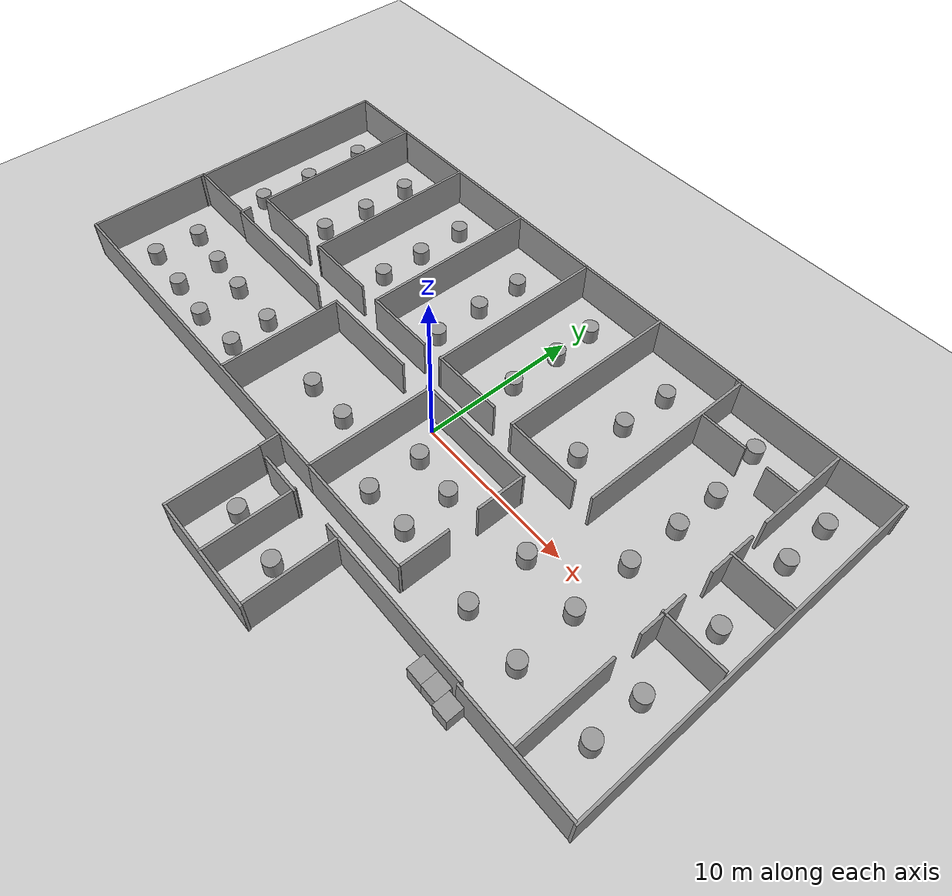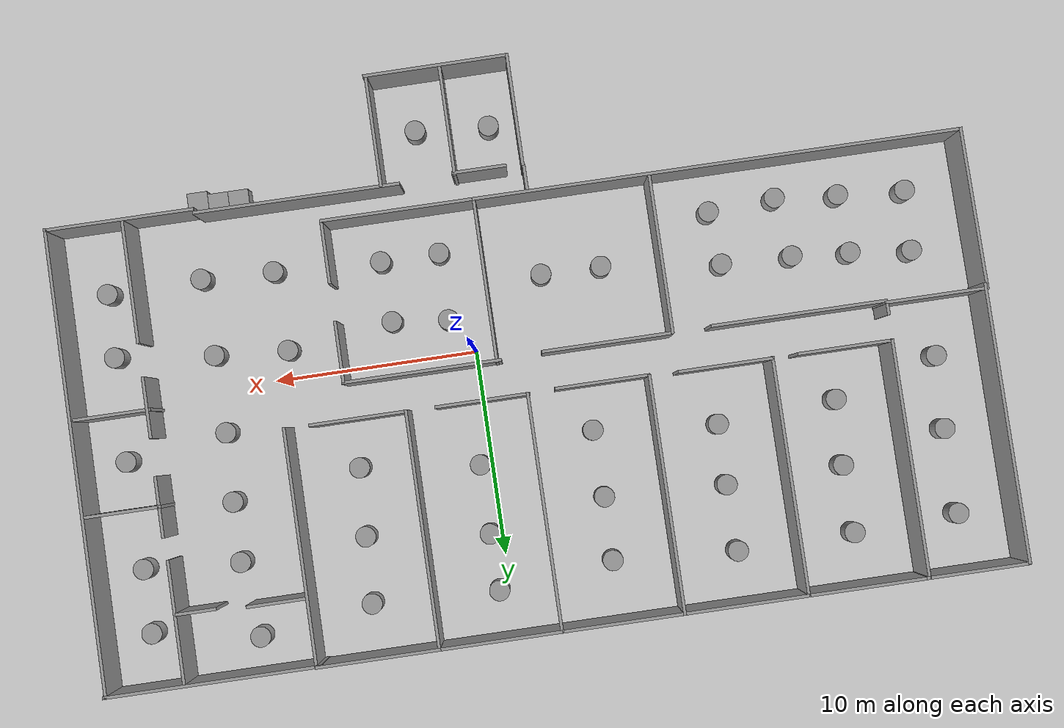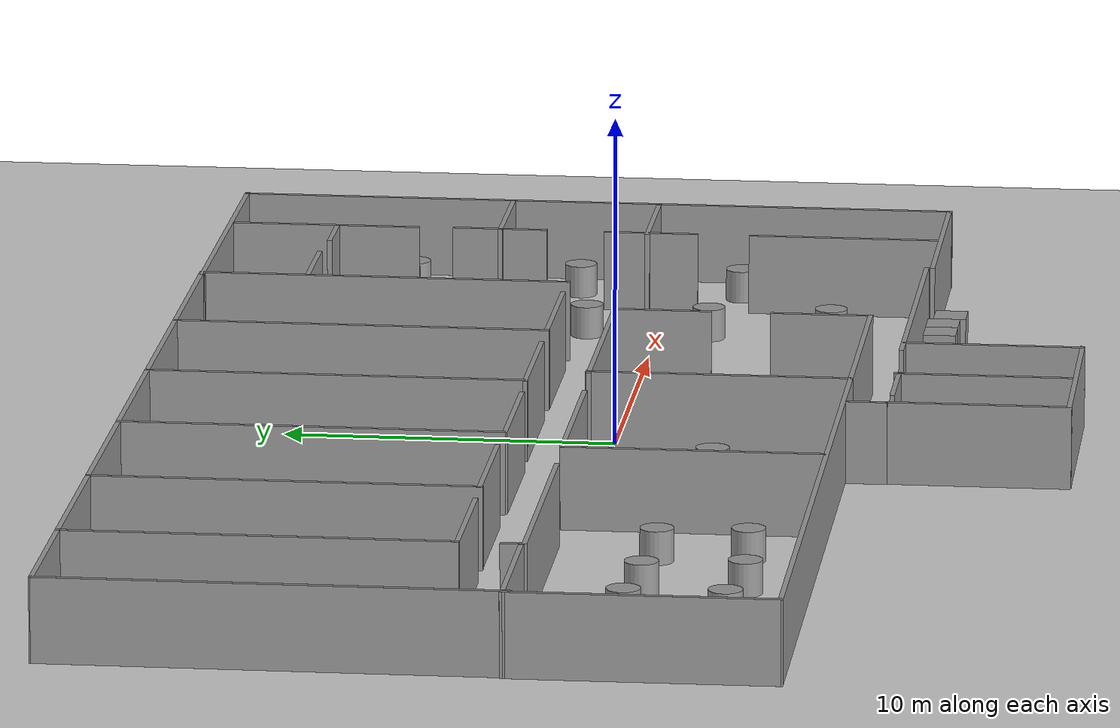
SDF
<sdf version="1.7">
 <world name="default">
  <light name="sun" type="directional">
   <pose>0 0 10 0 -0 0</pose>
   <diffuse>0.8 0.8 0.8 1</diffuse>
   <specular>0.2 0.2 0.2 1</specular>
   <attenuation>
    <range>1000</range>
    <constant>0.9</constant>
    <linear>0.01</linear>
    <quadratic>0.001</quadratic>
   </attenuation>
   <direction>-0.5 0.1 -0.9</direction>
   <spot><inner_angle>0</inner_angle><outer_angle>0</outer_angle><falloff>0</falloff></spot>
  </light>
  <model name="ground_plane">
   <static>1</static>
   <link name="link">
    <collision name="collision">
     <geometry><plane><normal>0 0 1</normal><size>100 100</size></plane></geometry>
     <surface>
      <contact><collide_bitmask>65535</collide_bitmask></contact>
      <friction><ode><mu>100</mu><mu2>50</mu2></ode></friction>
     </surface>
    </collision>
    <visual name="visual">
     <cast_shadows>0</cast_shadows>
     <geometry><plane><normal>0 0 1</normal><size>100 100</size></plane></geometry>
     <material>
      <script><uri>file://media/materials/scripts/gazebo.material</uri><name>Gazebo/Grey</name></script>
     </material>
    </visual>
   </link>
  </model>
  <gravity>0 0 -9.8</gravity>
  <magnetic_field>6e-06 2.3e-05 -4.2e-05</magnetic_field>
  <atmosphere type="adiabatic"/>
  <physics name="default_physics" default="0" type="ode">
   <max_step_size>0.001</max_step_size>
   <real_time_factor>1</real_time_factor>
   <real_time_update_rate>1000</real_time_update_rate>
  </physics>
  <scene><ambient>0.4 0.4 0.4 1</ambient><background>0.7 0.7 0.7 1</background><shadows>1</shadows></scene>
  <audio><device>default</device></audio>
  <spherical_coordinates>
   <surface_model>EARTH_WGS84</surface_model>
   <latitude_deg>0</latitude_deg>
   <longitude_deg>0</longitude_deg>
   <elevation>0</elevation>
   <heading_deg>0</heading_deg>
  </spherical_coordinates>
  <model name="5th_v2">
   <link name="Wall_101">
    <pose>19.5337 2.57533 0 0 0 -1.5708</pose>
    <visual name="Wall_101_Visual">
     <pose>0 0 1.25 0 -0 0</pose>
     <geometry><box><size>22.5 0.15 2.5</size></box></geometry>
     <material>
      <script><uri>file://media/materials/scripts/gazebo.material</uri><name>Gazebo/Grey</name></script>
      <ambient>1 1 1 1</ambient>
     </material>
     <meta><layer>0</layer></meta>
    </visual>
    <collision name="Wall_101_Collision">
     <pose>0 0 1.25 0 -0 0</pose>
     <geometry><box><size>22.5 0.15 2.5</size></box></geometry>
     <surface>
      <friction>
       <ode><mu>1</mu><mu2>1</mu2><fdir1>0 0 0</fdir1><slip1>0</slip1><slip2>0</slip2></ode>
       <torsional>
        <coefficient>1</coefficient>
        <patch_radius>0</patch_radius>
        <surface_radius>0</surface_radius>
        <use_patch_radius>1</use_patch_radius>
        <ode><slip>0</slip></ode>
       </torsional>
      </friction>
      <bounce><restitution_coefficient>0</restitution_coefficient><threshold>1e+06</threshold></bounce>
      <contact>
       <collide_without_contact>0</collide_without_contact>
       <collide_without_contact_bitmask>1</collide_without_contact_bitmask>
       <collide_bitmask>1</collide_bitmask>
       <ode>
        <soft_cfm>0</soft_cfm>
        <soft_erp>0.2</soft_erp>
        <kp>1e+13</kp>
        <kd>1</kd>
        <max_vel>0.01</max_vel>
        <min_depth>0</min_depth>
       </ode>
       <bullet>
        <split_impulse>1</split_impulse>
        <split_impulse_penetration_threshold>-0.01</split_impulse_penetration_threshold>
        <soft_cfm>0</soft_cfm>
        <soft_erp>0.2</soft_erp>
        <kp>1e+13</kp>
        <kd>1</kd>
       </bullet>
      </contact>
     </surface>
    </collision>
   </link>
   <link name="Wall_102">
    <pose>15.9331 -8.58282 0 0 -0 3.14159</pose>
    <inertial>
     <inertia><ixx>0</ixx><ixy>0</ixy><ixz>0</ixz><iyy>0</iyy><iyz>0</iyz><izz>0</izz></inertia>
     <mass>0</mass>
    </inertial>
    <visual name="Wall_102_Visual">
     <pose>0 0 1.25 0 -0 0</pose>
     <geometry><box><size>7.15162 0.15 2.5</size></box></geometry>
     <material>
      <script><uri>file://media/materials/scripts/gazebo.material</uri><name>Gazebo/Grey</name></script>
      <ambient>1 1 1 1</ambient>
     </material>
     <meta><layer>0</layer></meta>
    </visual>
    <collision name="Wall_102_Collision">
     <pose>0 0 1.25 0 -0 0</pose>
     <geometry><box><size>7.15162 0.15 2.5</size></box></geometry>
     <surface>
      <friction>
       <ode><mu>1</mu><mu2>1</mu2><fdir1>0 0 0</fdir1><slip1>0</slip1><slip2>0</slip2></ode>
       <torsional>
        <coefficient>1</coefficient>
        <patch_radius>0</patch_radius>
        <surface_radius>0</surface_radius>
        <use_patch_radius>1</use_patch_radius>
        <ode><slip>0</slip></ode>
       </torsional>
      </friction>
      <bounce><restitution_coefficient>0</restitution_coefficient><threshold>1e+06</threshold></bounce>
      <contact>
       <collide_without_contact>0</collide_without_contact>
       <collide_without_contact_bitmask>1</collide_without_contact_bitmask>
       <collide_bitmask>1</collide_bitmask>
       <ode>
        <soft_cfm>0</soft_cfm>
        <soft_erp>0.2</soft_erp>
        <kp>1e+13</kp>
        <kd>1</kd>
        <max_vel>0.01</max_vel>
        <min_depth>0</min_depth>
       </ode>
       <bullet>
        <split_impulse>1</split_impulse>
        <split_impulse_penetration_threshold>-0.01</split_impulse_penetration_threshold>
        <soft_cfm>0</soft_cfm>
        <soft_erp>0.2</soft_erp>
        <kp>1e+13</kp>
        <kd>1</kd>
       </bullet>
      </contact>
     </surface>
    </collision>
   </link>
   <link name="Wall_105">
    <pose>-3.56301 -7.81645 0 0 0 -1.5708</pose>
    <visual name="Wall_105_Visual">
     <pose>0 0 1.25 0 -0 0</pose>
     <geometry><box><size>1.25 0.15 2.5</size></box></geometry>
     <material>
      <script><uri>file://media/materials/scripts/gazebo.material</uri><name>Gazebo/Grey</name></script>
      <ambient>1 1 1 1</ambient>
     </material>
     <meta><layer>0</layer></meta>
    </visual>
    <collision name="Wall_105_Collision">
     <pose>0 0 1.25 0 -0 0</pose>
     <geometry><box><size>1.25 0.15 2.5</size></box></geometry>
     <surface>
      <friction>
       <ode><mu>1</mu><mu2>1</mu2><fdir1>0 0 0</fdir1><slip1>0</slip1><slip2>0</slip2></ode>
       <torsional>
        <coefficient>1</coefficient>
        <patch_radius>0</patch_radius>
        <surface_radius>0</surface_radius>
        <use_patch_radius>1</use_patch_radius>
        <ode><slip>0</slip></ode>
       </torsional>
      </friction>
      <bounce><restitution_coefficient>0</restitution_coefficient><threshold>1e+06</threshold></bounce>
      <contact>
       <collide_without_contact>0</collide_without_contact>
       <collide_without_contact_bitmask>1</collide_without_contact_bitmask>
       <collide_bitmask>1</collide_bitmask>
       <ode>
        <soft_cfm>0</soft_cfm>
        <soft_erp>0.2</soft_erp>
        <kp>1e+13</kp>
        <kd>1</kd>
        <max_vel>0.01</max_vel>
        <min_depth>0</min_depth>
       </ode>
       <bullet>
        <split_impulse>1</split_impulse>
        <split_impulse_penetration_threshold>-0.01</split_impulse_penetration_threshold>
        <soft_cfm>0</soft_cfm>
        <soft_erp>0.2</soft_erp>
        <kp>1e+13</kp>
        <kd>1</kd>
       </bullet>
      </contact>
     </surface>
    </collision>
   </link>
   <link name="Wall_108">
    <pose>15.8645 5.27903 0 0 -0 1.5708</pose>
    <inertial>
     <inertia><ixx>0</ixx><ixy>0</ixy><ixz>0</ixz><iyy>0</iyy><iyz>0</iyz><izz>0</izz></inertia>
     <mass>0</mass>
    </inertial>
    <visual name="Wall_108_Visual">
     <pose>0 0 1.25 0 -0 0</pose>
     <geometry><box><size>2.96394 0.15 2.5</size></box></geometry>
     <material>
      <script><uri>file://media/materials/scripts/gazebo.material</uri><name>Gazebo/Grey</name></script>
      <ambient>1 1 1 1</ambient>
     </material>
     <meta><layer>0</layer></meta>
    </visual>
    <collision name="Wall_108_Collision">
     <pose>0 0 1.25 0 -0 0</pose>
     <geometry><box><size>2.96394 0.15 2.5</size></box></geometry>
     <surface>
      <friction>
       <ode><mu>1</mu><mu2>1</mu2><fdir1>0 0 0</fdir1><slip1>0</slip1><slip2>0</slip2></ode>
       <torsional>
        <coefficient>1</coefficient>
        <patch_radius>0</patch_radius>
        <surface_radius>0</surface_radius>
        <use_patch_radius>1</use_patch_radius>
        <ode><slip>0</slip></ode>
       </torsional>
      </friction>
      <bounce><restitution_coefficient>0</restitution_coefficient><threshold>1e+06</threshold></bounce>
      <contact>
       <collide_without_contact>0</collide_without_contact>
       <collide_without_contact_bitmask>1</collide_without_contact_bitmask>
       <collide_bitmask>1</collide_bitmask>
       <ode>
        <soft_cfm>0</soft_cfm>
        <soft_erp>0.2</soft_erp>
        <kp>1e+13</kp>
        <kd>1</kd>
        <max_vel>0.01</max_vel>
        <min_depth>0</min_depth>
       </ode>
       <bullet>
        <split_impulse>1</split_impulse>
        <split_impulse_penetration_threshold>-0.01</split_impulse_penetration_threshold>
        <soft_cfm>0</soft_cfm>
        <soft_erp>0.2</soft_erp>
        <kp>1e+13</kp>
        <kd>1</kd>
       </bullet>
      </contact>
     </surface>
    </collision>
   </link>
   <link name="Wall_108_clone">
    <pose>15.8279 0.515353 0 0 -0 1.5708</pose>
    <inertial>
     <inertia><ixx>0</ixx><ixy>0</ixy><ixz>0</ixz><iyy>0</iyy><iyz>0</iyz><izz>0</izz></inertia>
     <mass>0</mass>
    </inertial>
    <visual name="Wall_108_Visual">
     <pose>0 0 1.25 0 -0 0</pose>
     <geometry><box><size>2.96394 0.15 2.5</size></box></geometry>
     <material>
      <script><uri>file://media/materials/scripts/gazebo.material</uri><name>Gazebo/Grey</name></script>
      <ambient>1 1 1 1</ambient>
      <shader type="pixel"/>
     </material>
     <meta><layer>0</layer></meta>
    </visual>
    <collision name="Wall_108_Collision">
     <pose>0 0 1.25 0 -0 0</pose>
     <geometry><box><size>2.96394 0.15 2.5</size></box></geometry>
     <surface>
      <friction>
       <ode><mu>1</mu><mu2>1</mu2><fdir1>0 0 0</fdir1><slip1>0</slip1><slip2>0</slip2></ode>
       <torsional>
        <coefficient>1</coefficient>
        <patch_radius>0</patch_radius>
        <surface_radius>0</surface_radius>
        <use_patch_radius>1</use_patch_radius>
        <ode><slip>0</slip></ode>
       </torsional>
      </friction>
      <bounce><restitution_coefficient>0</restitution_coefficient><threshold>1e+06</threshold></bounce>
      <contact>
       <collide_without_contact>0</collide_without_contact>
       <collide_without_contact_bitmask>1</collide_without_contact_bitmask>
       <collide_bitmask>1</collide_bitmask>
       <ode>
        <soft_cfm>0</soft_cfm>
        <soft_erp>0.2</soft_erp>
        <kp>1e+13</kp>
        <kd>1</kd>
        <max_vel>0.01</max_vel>
        <min_depth>0</min_depth>
       </ode>
       <bullet>
        <split_impulse>1</split_impulse>
        <split_impulse_penetration_threshold>-0.01</split_impulse_penetration_threshold>
        <soft_cfm>0</soft_cfm>
        <soft_erp>0.2</soft_erp>
        <kp>1e+13</kp>
        <kd>1</kd>
       </bullet>
      </contact>
     </surface>
    </collision>
   </link>
   <link name="Wall_108_clone_0">
    <pose>15.8288 -5.57913 0 0 -0 1.5708</pose>
    <inertial>
     <inertia><ixx>0</ixx><ixy>0</ixy><ixz>0</ixz><iyy>0</iyy><iyz>0</iyz><izz>0</izz></inertia>
     <mass>0</mass>
    </inertial>
    <visual name="Wall_108_Visual">
     <pose>0 0 1.25 0 -0 0</pose>
     <geometry><box><size>6.01082 0.15 2.5</size></box></geometry>
     <material>
      <script><uri>file://media/materials/scripts/gazebo.material</uri><name>Gazebo/Grey</name></script>
      <ambient>1 1 1 1</ambient>
      <shader type="pixel"/>
     </material>
     <meta><layer>0</layer></meta>
    </visual>
    <collision name="Wall_108_Collision">
     <pose>0 0 1.25 0 -0 0</pose>
     <geometry><box><size>6.01082 0.15 2.5</size></box></geometry>
     <surface>
      <friction>
       <ode><mu>1</mu><mu2>1</mu2><fdir1>0 0 0</fdir1><slip1>0</slip1><slip2>0</slip2></ode>
       <torsional>
        <coefficient>1</coefficient>
        <patch_radius>0</patch_radius>
        <surface_radius>0</surface_radius>
        <use_patch_radius>1</use_patch_radius>
        <ode><slip>0</slip></ode>
       </torsional>
      </friction>
      <bounce><restitution_coefficient>0</restitution_coefficient><threshold>1e+06</threshold></bounce>
      <contact>
       <collide_without_contact>0</collide_without_contact>
       <collide_without_contact_bitmask>1</collide_without_contact_bitmask>
       <collide_bitmask>1</collide_bitmask>
       <ode>
        <soft_cfm>0</soft_cfm>
        <soft_erp>0.2</soft_erp>
        <kp>1e+13</kp>
        <kd>1</kd>
        <max_vel>0.01</max_vel>
        <min_depth>0</min_depth>
       </ode>
       <bullet>
        <split_impulse>1</split_impulse>
        <split_impulse_penetration_threshold>-0.01</split_impulse_penetration_threshold>
        <soft_cfm>0</soft_cfm>
        <soft_erp>0.2</soft_erp>
        <kp>1e+13</kp>
        <kd>1</kd>
       </bullet>
      </contact>
     </surface>
    </collision>
   </link>
   <link name="Wall_108_clone_1">
    <pose>15.7933 10.8016 0 0 -0 1.5708</pose>
    <inertial>
     <inertia><ixx>0</ixx><ixy>0</ixy><ixz>0</ixz><iyy>0</iyy><iyz>0</iyz><izz>0</izz></inertia>
     <mass>0</mass>
    </inertial>
    <visual name="Wall_108_Visual">
     <pose>0 0 1.25 0 -0 0</pose>
     <geometry><box><size>5.97377 0.15 2.5</size></box></geometry>
     <material>
      <script><uri>file://media/materials/scripts/gazebo.material</uri><name>Gazebo/Grey</name></script>
      <ambient>1 1 1 1</ambient>
      <shader type="pixel"/>
     </material>
     <meta><layer>0</layer></meta>
    </visual>
    <collision name="Wall_108_Collision">
     <pose>0 0 1.25 0 -0 0</pose>
     <geometry><box><size>5.97377 0.15 2.5</size></box></geometry>
     <surface>
      <friction>
       <ode><mu>1</mu><mu2>1</mu2><fdir1>0 0 0</fdir1><slip1>0</slip1><slip2>0</slip2></ode>
       <torsional>
        <coefficient>1</coefficient>
        <patch_radius>0</patch_radius>
        <surface_radius>0</surface_radius>
        <use_patch_radius>1</use_patch_radius>
        <ode><slip>0</slip></ode>
       </torsional>
      </friction>
      <bounce><restitution_coefficient>0</restitution_coefficient><threshold>1e+06</threshold></bounce>
      <contact>
       <collide_without_contact>0</collide_without_contact>
       <collide_without_contact_bitmask>1</collide_without_contact_bitmask>
       <collide_bitmask>1</collide_bitmask>
       <ode>
        <soft_cfm>0</soft_cfm>
        <soft_erp>0.2</soft_erp>
        <kp>1e+13</kp>
        <kd>1</kd>
        <max_vel>0.01</max_vel>
        <min_depth>0</min_depth>
       </ode>
       <bullet>
        <split_impulse>1</split_impulse>
        <split_impulse_penetration_threshold>-0.01</split_impulse_penetration_threshold>
        <soft_cfm>0</soft_cfm>
        <soft_erp>0.2</soft_erp>
        <kp>1e+13</kp>
        <kd>1</kd>
       </bullet>
      </contact>
     </surface>
    </collision>
   </link>
   <link name="Wall_108_clone_clone">
    <pose>6.41093 -0.803869 0 0 -0 1.5708</pose>
    <inertial>
     <inertia><ixx>0</ixx><ixy>0</ixy><ixz>0</ixz><iyy>0</iyy><iyz>0</iyz><izz>0</izz></inertia>
     <mass>0</mass>
    </inertial>
    <visual name="Wall_108_Visual">
     <pose>0 0 1.25 0 -0 0</pose>
     <geometry><box><size>2.96394 0.15 2.5</size></box></geometry>
     <material>
      <script><uri>file://media/materials/scripts/gazebo.material</uri><name>Gazebo/Grey</name></script>
      <ambient>1 1 1 1</ambient>
      <shader type="pixel"/>
     </material>
     <meta><layer>0</layer></meta>
    </visual>
    <collision name="Wall_108_Collision">
     <pose>0 0 1.25 0 -0 0</pose>
     <geometry><box><size>2.96394 0.15 2.5</size></box></geometry>
     <surface>
      <friction>
       <ode><mu>1</mu><mu2>1</mu2><fdir1>0 0 0</fdir1><slip1>0</slip1><slip2>0</slip2></ode>
       <torsional>
        <coefficient>1</coefficient>
        <patch_radius>0</patch_radius>
        <surface_radius>0</surface_radius>
        <use_patch_radius>1</use_patch_radius>
        <ode><slip>0</slip></ode>
       </torsional>
      </friction>
      <bounce><restitution_coefficient>0</restitution_coefficient><threshold>1e+06</threshold></bounce>
      <contact>
       <collide_without_contact>0</collide_without_contact>
       <collide_without_contact_bitmask>1</collide_without_contact_bitmask>
       <collide_bitmask>1</collide_bitmask>
       <ode>
        <soft_cfm>0</soft_cfm>
        <soft_erp>0.2</soft_erp>
        <kp>1e+13</kp>
        <kd>1</kd>
        <max_vel>0.01</max_vel>
        <min_depth>0</min_depth>
       </ode>
       <bullet>
        <split_impulse>1</split_impulse>
        <split_impulse_penetration_threshold>-0.01</split_impulse_penetration_threshold>
        <soft_cfm>0</soft_cfm>
        <soft_erp>0.2</soft_erp>
        <kp>1e+13</kp>
        <kd>1</kd>
       </bullet>
      </contact>
     </surface>
    </collision>
   </link>
   <link name="Wall_108_clone_clone_0">
    <pose>6.41093 -5.56687 0 0 -0 1.5708</pose>
    <inertial>
     <inertia><ixx>0</ixx><ixy>0</ixy><ixz>0</ixz><iyy>0</iyy><iyz>0</iyz><izz>0</izz></inertia>
     <mass>0</mass>
    </inertial>
    <visual name="Wall_108_Visual">
     <pose>0 0 1.25 0 -0 0</pose>
     <geometry><box><size>2.96394 0.15 2.5</size></box></geometry>
     <material>
      <script><uri>file://media/materials/scripts/gazebo.material</uri><name>Gazebo/Grey</name></script>
      <ambient>1 1 1 1</ambient>
      <shader type="pixel"/>
     </material>
     <meta><layer>0</layer></meta>
    </visual>
    <collision name="Wall_108_Collision">
     <pose>0 0 1.25 0 -0 0</pose>
     <geometry><box><size>2.96394 0.15 2.5</size></box></geometry>
     <surface>
      <friction>
       <ode><mu>1</mu><mu2>1</mu2><fdir1>0 0 0</fdir1><slip1>0</slip1><slip2>0</slip2></ode>
       <torsional>
        <coefficient>1</coefficient>
        <patch_radius>0</patch_radius>
        <surface_radius>0</surface_radius>
        <use_patch_radius>1</use_patch_radius>
        <ode><slip>0</slip></ode>
       </torsional>
      </friction>
      <bounce><restitution_coefficient>0</restitution_coefficient><threshold>1e+06</threshold></bounce>
      <contact>
       <collide_without_contact>0</collide_without_contact>
       <collide_without_contact_bitmask>1</collide_without_contact_bitmask>
       <collide_bitmask>1</collide_bitmask>
       <ode>
        <soft_cfm>0</soft_cfm>
        <soft_erp>0.2</soft_erp>
        <kp>1e+13</kp>
        <kd>1</kd>
        <max_vel>0.01</max_vel>
        <min_depth>0</min_depth>
       </ode>
       <bullet>
        <split_impulse>1</split_impulse>
        <split_impulse_penetration_threshold>-0.01</split_impulse_penetration_threshold>
        <soft_cfm>0</soft_cfm>
        <soft_erp>0.2</soft_erp>
        <kp>1e+13</kp>
        <kd>1</kd>
       </bullet>
      </contact>
     </surface>
    </collision>
   </link>
   <link name="Wall_114">
    <pose>17.6178 5.25914 0 0 -0 0</pose>
    <inertial>
     <inertia><ixx>0</ixx><ixy>0</ixy><ixz>0</ixz><iyy>0</iyy><iyz>0</iyz><izz>0</izz></inertia>
     <mass>0</mass>
    </inertial>
    <visual name="Wall_114_Visual">
     <pose>0 0 1.25 0 -0 0</pose>
     <geometry><box><size>3.72578 0.15 2.5</size></box></geometry>
     <material>
      <script><uri>file://media/materials/scripts/gazebo.material</uri><name>Gazebo/Grey</name></script>
      <ambient>1 1 1 1</ambient>
     </material>
     <meta><layer>0</layer></meta>
    </visual>
    <collision name="Wall_114_Collision">
     <pose>0 0 1.25 0 -0 0</pose>
     <geometry><box><size>3.72578 0.15 2.5</size></box></geometry>
     <surface>
      <friction>
       <ode><mu>1</mu><mu2>1</mu2><fdir1>0 0 0</fdir1><slip1>0</slip1><slip2>0</slip2></ode>
       <torsional>
        <coefficient>1</coefficient>
        <patch_radius>0</patch_radius>
        <surface_radius>0</surface_radius>
        <use_patch_radius>1</use_patch_radius>
        <ode><slip>0</slip></ode>
       </torsional>
      </friction>
      <bounce><restitution_coefficient>0</restitution_coefficient><threshold>1e+06</threshold></bounce>
      <contact>
       <collide_without_contact>0</collide_without_contact>
       <collide_without_contact_bitmask>1</collide_without_contact_bitmask>
       <collide_bitmask>1</collide_bitmask>
       <ode>
        <soft_cfm>0</soft_cfm>
        <soft_erp>0.2</soft_erp>
        <kp>1e+13</kp>
        <kd>1</kd>
        <max_vel>0.01</max_vel>
        <min_depth>0</min_depth>
       </ode>
       <bullet>
        <split_impulse>1</split_impulse>
        <split_impulse_penetration_threshold>-0.01</split_impulse_penetration_threshold>
        <soft_cfm>0</soft_cfm>
        <soft_erp>0.2</soft_erp>
        <kp>1e+13</kp>
        <kd>1</kd>
       </bullet>
      </contact>
     </surface>
    </collision>
   </link>
   <link name="Wall_114_clone">
    <pose>17.5188 0.617185 0 0 -0 0</pose>
    <inertial>
     <inertia><ixx>0</ixx><ixy>0</ixy><ixz>0</ixz><iyy>0</iyy><iyz>0</iyz><izz>0</izz></inertia>
     <mass>0</mass>
    </inertial>
    <visual name="Wall_114_Visual">
     <pose>0 0 1.25 0 -0 0</pose>
     <geometry><box><size>3.72578 0.15 2.5</size></box></geometry>
     <material>
      <script><uri>file://media/materials/scripts/gazebo.material</uri><name>Gazebo/Grey</name></script>
      <ambient>1 1 1 1</ambient>
      <shader type="pixel"/>
     </material>
     <meta><layer>0</layer></meta>
    </visual>
    <collision name="Wall_114_Collision">
     <pose>0 0 1.25 0 -0 0</pose>
     <geometry><box><size>3.72578 0.15 2.5</size></box></geometry>
     <surface>
      <friction>
       <ode><mu>1</mu><mu2>1</mu2><fdir1>0 0 0</fdir1><slip1>0</slip1><slip2>0</slip2></ode>
       <torsional>
        <coefficient>1</coefficient>
        <patch_radius>0</patch_radius>
        <surface_radius>0</surface_radius>
        <use_patch_radius>1</use_patch_radius>
        <ode><slip>0</slip></ode>
       </torsional>
      </friction>
      <bounce><restitution_coefficient>0</restitution_coefficient><threshold>1e+06</threshold></bounce>
      <contact>
       <collide_without_contact>0</collide_without_contact>
       <collide_without_contact_bitmask>1</collide_without_contact_bitmask>
       <collide_bitmask>1</collide_bitmask>
       <ode>
        <soft_cfm>0</soft_cfm>
        <soft_erp>0.2</soft_erp>
        <kp>1e+13</kp>
        <kd>1</kd>
        <max_vel>0.01</max_vel>
        <min_depth>0</min_depth>
       </ode>
       <bullet>
        <split_impulse>1</split_impulse>
        <split_impulse_penetration_threshold>-0.01</split_impulse_penetration_threshold>
        <soft_cfm>0</soft_cfm>
        <soft_erp>0.2</soft_erp>
        <kp>1e+13</kp>
        <kd>1</kd>
       </bullet>
      </contact>
     </surface>
    </collision>
   </link>
   <link name="Wall_114_clone_0">
    <pose>10.9394 10.5296 0 0 -0 0</pose>
    <inertial>
     <inertia><ixx>0</ixx><ixy>0</ixy><ixz>0</ixz><iyy>0</iyy><iyz>0</iyz><izz>0</izz></inertia>
     <mass>0</mass>
    </inertial>
    <visual name="Wall_114_Visual">
     <pose>0 0 1.25 0 -0 0</pose>
     <geometry><box><size>2.97072 0.15 2.5</size></box></geometry>
     <material>
      <script><uri>file://media/materials/scripts/gazebo.material</uri><name>Gazebo/Grey</name></script>
      <ambient>1 1 1 1</ambient>
      <shader type="pixel"/>
     </material>
     <meta><layer>0</layer></meta>
    </visual>
    <collision name="Wall_114_Collision">
     <pose>0 0 1.25 0 -0 0</pose>
     <geometry><box><size>2.97072 0.15 2.5</size></box></geometry>
     <surface>
      <friction>
       <ode><mu>1</mu><mu2>1</mu2><fdir1>0 0 0</fdir1><slip1>0</slip1><slip2>0</slip2></ode>
       <torsional>
        <coefficient>1</coefficient>
        <patch_radius>0</patch_radius>
        <surface_radius>0</surface_radius>
        <use_patch_radius>1</use_patch_radius>
        <ode><slip>0</slip></ode>
       </torsional>
      </friction>
      <bounce><restitution_coefficient>0</restitution_coefficient><threshold>1e+06</threshold></bounce>
      <contact>
       <collide_without_contact>0</collide_without_contact>
       <collide_without_contact_bitmask>1</collide_without_contact_bitmask>
       <collide_bitmask>1</collide_bitmask>
       <ode>
        <soft_cfm>0</soft_cfm>
        <soft_erp>0.2</soft_erp>
        <kp>1e+13</kp>
        <kd>1</kd>
        <max_vel>0.01</max_vel>
        <min_depth>0</min_depth>
       </ode>
       <bullet>
        <split_impulse>1</split_impulse>
        <split_impulse_penetration_threshold>-0.01</split_impulse_penetration_threshold>
        <soft_cfm>0</soft_cfm>
        <soft_erp>0.2</soft_erp>
        <kp>1e+13</kp>
        <kd>1</kd>
       </bullet>
      </contact>
     </surface>
    </collision>
   </link>
   <link name="Wall_114_clone_0_clone">
    <pose>14.7944 10.4041 0 0 -0 0</pose>
    <inertial>
     <inertia><ixx>0</ixx><ixy>0</ixy><ixz>0</ixz><iyy>0</iyy><iyz>0</iyz><izz>0</izz></inertia>
     <mass>0</mass>
    </inertial>
    <visual name="Wall_114_Visual">
     <pose>0 0 1.25 0 -0 0</pose>
     <geometry><box><size>1.96716 0.15 2.5</size></box></geometry>
     <material>
      <script><uri>file://media/materials/scripts/gazebo.material</uri><name>Gazebo/Grey</name></script>
      <ambient>1 1 1 1</ambient>
      <shader type="pixel"/>
     </material>
     <meta><layer>0</layer></meta>
    </visual>
    <collision name="Wall_114_Collision">
     <pose>0 0 1.25 0 -0 0</pose>
     <geometry><box><size>1.96716 0.15 2.5</size></box></geometry>
     <surface>
      <friction>
       <ode><mu>1</mu><mu2>1</mu2><fdir1>0 0 0</fdir1><slip1>0</slip1><slip2>0</slip2></ode>
       <torsional>
        <coefficient>1</coefficient>
        <patch_radius>0</patch_radius>
        <surface_radius>0</surface_radius>
        <use_patch_radius>1</use_patch_radius>
        <ode><slip>0</slip></ode>
       </torsional>
      </friction>
      <bounce><restitution_coefficient>0</restitution_coefficient><threshold>1e+06</threshold></bounce>
      <contact>
       <collide_without_contact>0</collide_without_contact>
       <collide_without_contact_bitmask>1</collide_without_contact_bitmask>
       <collide_bitmask>1</collide_bitmask>
       <ode>
        <soft_cfm>0</soft_cfm>
        <soft_erp>0.2</soft_erp>
        <kp>1e+13</kp>
        <kd>1</kd>
        <max_vel>0.01</max_vel>
        <min_depth>0</min_depth>
       </ode>
       <bullet>
        <split_impulse>1</split_impulse>
        <split_impulse_penetration_threshold>-0.01</split_impulse_penetration_threshold>
        <soft_cfm>0</soft_cfm>
        <soft_erp>0.2</soft_erp>
        <kp>1e+13</kp>
        <kd>1</kd>
       </bullet>
      </contact>
     </surface>
    </collision>
   </link>
   <link name="Wall_19">
    <pose>-13.9677 8.12089 0 0 0 -1.5708</pose>
    <visual name="Wall_19_Visual">
     <pose>0 0 1.25 0 -0 0</pose>
     <geometry><box><size>11.5 0.15 2.5</size></box></geometry>
     <material>
      <script><uri>file://media/materials/scripts/gazebo.material</uri><name>Gazebo/Grey</name></script>
      <ambient>1 1 1 1</ambient>
     </material>
     <meta><layer>0</layer></meta>
    </visual>
    <collision name="Wall_19_Collision">
     <pose>0 0 1.25 0 -0 0</pose>
     <geometry><box><size>11.5 0.15 2.5</size></box></geometry>
     <surface>
      <friction>
       <ode><mu>1</mu><mu2>1</mu2><fdir1>0 0 0</fdir1><slip1>0</slip1><slip2>0</slip2></ode>
       <torsional>
        <coefficient>1</coefficient>
        <patch_radius>0</patch_radius>
        <surface_radius>0</surface_radius>
        <use_patch_radius>1</use_patch_radius>
        <ode><slip>0</slip></ode>
       </torsional>
      </friction>
      <bounce><restitution_coefficient>0</restitution_coefficient><threshold>1e+06</threshold></bounce>
      <contact>
       <collide_without_contact>0</collide_without_contact>
       <collide_without_contact_bitmask>1</collide_without_contact_bitmask>
       <collide_bitmask>1</collide_bitmask>
       <ode>
        <soft_cfm>0</soft_cfm>
        <soft_erp>0.2</soft_erp>
        <kp>1e+13</kp>
        <kd>1</kd>
        <max_vel>0.01</max_vel>
        <min_depth>0</min_depth>
       </ode>
       <bullet>
        <split_impulse>1</split_impulse>
        <split_impulse_penetration_threshold>-0.01</split_impulse_penetration_threshold>
        <soft_cfm>0</soft_cfm>
        <soft_erp>0.2</soft_erp>
        <kp>1e+13</kp>
        <kd>1</kd>
       </bullet>
      </contact>
     </surface>
    </collision>
   </link>
   <link name="Wall_21">
    <pose>-8.03913 8.13641 0 0 -0 1.5708</pose>
    <visual name="Wall_21_Visual">
     <pose>0 0 1.25 0 -0 0</pose>
     <geometry><box><size>11.5 0.15 2.5</size></box></geometry>
     <material>
      <script><uri>file://media/materials/scripts/gazebo.material</uri><name>Gazebo/Grey</name></script>
      <ambient>1 1 1 1</ambient>
     </material>
     <meta><layer>0</layer></meta>
    </visual>
    <collision name="Wall_21_Collision">
     <pose>0 0 1.25 0 -0 0</pose>
     <geometry><box><size>11.5 0.15 2.5</size></box></geometry>
     <surface>
      <friction>
       <ode><mu>1</mu><mu2>1</mu2><fdir1>0 0 0</fdir1><slip1>0</slip1><slip2>0</slip2></ode>
       <torsional>
        <coefficient>1</coefficient>
        <patch_radius>0</patch_radius>
        <surface_radius>0</surface_radius>
        <use_patch_radius>1</use_patch_radius>
        <ode><slip>0</slip></ode>
       </torsional>
      </friction>
      <bounce><restitution_coefficient>0</restitution_coefficient><threshold>1e+06</threshold></bounce>
      <contact>
       <collide_without_contact>0</collide_without_contact>
       <collide_without_contact_bitmask>1</collide_without_contact_bitmask>
       <collide_bitmask>1</collide_bitmask>
       <ode>
        <soft_cfm>0</soft_cfm>
        <soft_erp>0.2</soft_erp>
        <kp>1e+13</kp>
        <kd>1</kd>
        <max_vel>0.01</max_vel>
        <min_depth>0</min_depth>
       </ode>
       <bullet>
        <split_impulse>1</split_impulse>
        <split_impulse_penetration_threshold>-0.01</split_impulse_penetration_threshold>
        <soft_cfm>0</soft_cfm>
        <soft_erp>0.2</soft_erp>
        <kp>1e+13</kp>
        <kd>1</kd>
       </bullet>
      </contact>
     </surface>
    </collision>
   </link>
   <link name="Wall_29">
    <pose>-19.7343 8.13641 0 0 -0 1.5708</pose>
    <visual name="Wall_29_Visual">
     <pose>0 0 1.25 0 -0 0</pose>
     <geometry><box><size>11.5 0.15 2.5</size></box></geometry>
     <material>
      <script><uri>file://media/materials/scripts/gazebo.material</uri><name>Gazebo/Grey</name></script>
      <ambient>1 1 1 1</ambient>
     </material>
     <meta><layer>0</layer></meta>
    </visual>
    <collision name="Wall_29_Collision">
     <pose>0 0 1.25 0 -0 0</pose>
     <geometry><box><size>11.5 0.15 2.5</size></box></geometry>
     <surface>
      <friction>
       <ode><mu>1</mu><mu2>1</mu2><fdir1>0 0 0</fdir1><slip1>0</slip1><slip2>0</slip2></ode>
       <torsional>
        <coefficient>1</coefficient>
        <patch_radius>0</patch_radius>
        <surface_radius>0</surface_radius>
        <use_patch_radius>1</use_patch_radius>
        <ode><slip>0</slip></ode>
       </torsional>
      </friction>
      <bounce><restitution_coefficient>0</restitution_coefficient><threshold>1e+06</threshold></bounce>
      <contact>
       <collide_without_contact>0</collide_without_contact>
       <collide_without_contact_bitmask>1</collide_without_contact_bitmask>
       <collide_bitmask>1</collide_bitmask>
       <ode>
        <soft_cfm>0</soft_cfm>
        <soft_erp>0.2</soft_erp>
        <kp>1e+13</kp>
        <kd>1</kd>
        <max_vel>0.01</max_vel>
        <min_depth>0</min_depth>
       </ode>
       <bullet>
        <split_impulse>1</split_impulse>
        <split_impulse_penetration_threshold>-0.01</split_impulse_penetration_threshold>
        <soft_cfm>0</soft_cfm>
        <soft_erp>0.2</soft_erp>
        <kp>1e+13</kp>
        <kd>1</kd>
       </bullet>
      </contact>
     </surface>
    </collision>
   </link>
   <link name="Wall_32">
    <pose>-2.18428 8.13641 0 0 -0 1.5708</pose>
    <visual name="Wall_32_Visual">
     <pose>0 0 1.25 0 -0 0</pose>
     <geometry><box><size>11.5 0.15 2.5</size></box></geometry>
     <material>
      <script><uri>file://media/materials/scripts/gazebo.material</uri><name>Gazebo/Grey</name></script>
      <ambient>1 1 1 1</ambient>
     </material>
     <meta><layer>0</layer></meta>
    </visual>
    <collision name="Wall_32_Collision">
     <pose>0 0 1.25 0 -0 0</pose>
     <geometry><box><size>11.5 0.15 2.5</size></box></geometry>
     <surface>
      <friction>
       <ode><mu>1</mu><mu2>1</mu2><fdir1>0 0 0</fdir1><slip1>0</slip1><slip2>0</slip2></ode>
       <torsional>
        <coefficient>1</coefficient>
        <patch_radius>0</patch_radius>
        <surface_radius>0</surface_radius>
        <use_patch_radius>1</use_patch_radius>
        <ode><slip>0</slip></ode>
       </torsional>
      </friction>
      <bounce><restitution_coefficient>0</restitution_coefficient><threshold>1e+06</threshold></bounce>
      <contact>
       <collide_without_contact>0</collide_without_contact>
       <collide_without_contact_bitmask>1</collide_without_contact_bitmask>
       <collide_bitmask>1</collide_bitmask>
       <ode>
        <soft_cfm>0</soft_cfm>
        <soft_erp>0.2</soft_erp>
        <kp>1e+13</kp>
        <kd>1</kd>
        <max_vel>0.01</max_vel>
        <min_depth>0</min_depth>
       </ode>
       <bullet>
        <split_impulse>1</split_impulse>
        <split_impulse_penetration_threshold>-0.01</split_impulse_penetration_threshold>
        <soft_cfm>0</soft_cfm>
        <soft_erp>0.2</soft_erp>
        <kp>1e+13</kp>
        <kd>1</kd>
       </bullet>
      </contact>
     </surface>
    </collision>
   </link>
   <link name="Wall_35">
    <pose>-19.7655 0.877576 0 0 0 -1.5708</pose>
    <inertial>
     <inertia><ixx>0</ixx><ixy>0</ixy><ixz>0</ixz><iyy>0</iyy><iyz>0</iyz><izz>0</izz></inertia>
     <mass>0</mass>
    </inertial>
    <visual name="Wall_35_Visual">
     <pose>0 0 1.25 0 -0 0</pose>
     <geometry><box><size>0.682332 0.15 2.5</size></box></geometry>
     <material>
      <script><uri>file://media/materials/scripts/gazebo.material</uri><name>Gazebo/Grey</name></script>
      <ambient>1 1 1 1</ambient>
     </material>
     <meta><layer>0</layer></meta>
    </visual>
    <collision name="Wall_35_Collision">
     <pose>0 0 1.25 0 -0 0</pose>
     <geometry><box><size>0.682332 0.15 2.5</size></box></geometry>
     <surface>
      <friction>
       <ode><mu>1</mu><mu2>1</mu2><fdir1>0 0 0</fdir1><slip1>0</slip1><slip2>0</slip2></ode>
       <torsional>
        <coefficient>1</coefficient>
        <patch_radius>0</patch_radius>
        <surface_radius>0</surface_radius>
        <use_patch_radius>1</use_patch_radius>
        <ode><slip>0</slip></ode>
       </torsional>
      </friction>
      <bounce><restitution_coefficient>0</restitution_coefficient><threshold>1e+06</threshold></bounce>
      <contact>
       <collide_without_contact>0</collide_without_contact>
       <collide_without_contact_bitmask>1</collide_without_contact_bitmask>
       <collide_bitmask>1</collide_bitmask>
       <ode>
        <soft_cfm>0</soft_cfm>
        <soft_erp>0.2</soft_erp>
        <kp>1e+13</kp>
        <kd>1</kd>
        <max_vel>0.01</max_vel>
        <min_depth>0</min_depth>
       </ode>
       <bullet>
        <split_impulse>1</split_impulse>
        <split_impulse_penetration_threshold>-0.01</split_impulse_penetration_threshold>
        <soft_cfm>0</soft_cfm>
        <soft_erp>0.2</soft_erp>
        <kp>1e+13</kp>
        <kd>1</kd>
       </bullet>
      </contact>
     </surface>
    </collision>
   </link>
   <link name="Wall_42">
    <pose>3.66572 8.13641 0 0 -0 1.5708</pose>
    <visual name="Wall_42_Visual">
     <pose>0 0 1.25 0 -0 0</pose>
     <geometry><box><size>11.5 0.15 2.5</size></box></geometry>
     <material>
      <script><uri>file://media/materials/scripts/gazebo.material</uri><name>Gazebo/Grey</name></script>
      <ambient>1 1 1 1</ambient>
     </material>
     <meta><layer>0</layer></meta>
    </visual>
    <collision name="Wall_42_Collision">
     <pose>0 0 1.25 0 -0 0</pose>
     <geometry><box><size>11.5 0.15 2.5</size></box></geometry>
     <surface>
      <friction>
       <ode><mu>1</mu><mu2>1</mu2><fdir1>0 0 0</fdir1><slip1>0</slip1><slip2>0</slip2></ode>
       <torsional>
        <coefficient>1</coefficient>
        <patch_radius>0</patch_radius>
        <surface_radius>0</surface_radius>
        <use_patch_radius>1</use_patch_radius>
        <ode><slip>0</slip></ode>
       </torsional>
      </friction>
      <bounce><restitution_coefficient>0</restitution_coefficient><threshold>1e+06</threshold></bounce>
      <contact>
       <collide_without_contact>0</collide_without_contact>
       <collide_without_contact_bitmask>1</collide_without_contact_bitmask>
       <collide_bitmask>1</collide_bitmask>
       <ode>
        <soft_cfm>0</soft_cfm>
        <soft_erp>0.2</soft_erp>
        <kp>1e+13</kp>
        <kd>1</kd>
        <max_vel>0.01</max_vel>
        <min_depth>0</min_depth>
       </ode>
       <bullet>
        <split_impulse>1</split_impulse>
        <split_impulse_penetration_threshold>-0.01</split_impulse_penetration_threshold>
        <soft_cfm>0</soft_cfm>
        <soft_erp>0.2</soft_erp>
        <kp>1e+13</kp>
        <kd>1</kd>
       </bullet>
      </contact>
     </surface>
    </collision>
   </link>
   <link name="Wall_44">
    <pose>-15.5505 0.526898 0 0 -0 0</pose>
    <inertial>
     <inertia><ixx>0</ixx><ixy>0</ixy><ixz>0</ixz><iyy>0</iyy><iyz>0</iyz><izz>0</izz></inertia>
     <mass>0</mass>
    </inertial>
    <visual name="Wall_44_Visual">
     <pose>0 0 1.25 0 -0 0</pose>
     <geometry><box><size>8.51811 0.15 2.5</size></box></geometry>
     <material>
      <script><uri>file://media/materials/scripts/gazebo.material</uri><name>Gazebo/Grey</name></script>
      <ambient>1 1 1 1</ambient>
     </material>
     <meta><layer>0</layer></meta>
    </visual>
    <collision name="Wall_44_Collision">
     <pose>0 0 1.25 0 -0 0</pose>
     <geometry><box><size>8.51811 0.15 2.5</size></box></geometry>
     <surface>
      <friction>
       <ode><mu>1</mu><mu2>1</mu2><fdir1>0 0 0</fdir1><slip1>0</slip1><slip2>0</slip2></ode>
       <torsional>
        <coefficient>1</coefficient>
        <patch_radius>0</patch_radius>
        <surface_radius>0</surface_radius>
        <use_patch_radius>1</use_patch_radius>
        <ode><slip>0</slip></ode>
       </torsional>
      </friction>
      <bounce><restitution_coefficient>0</restitution_coefficient><threshold>1e+06</threshold></bounce>
      <contact>
       <collide_without_contact>0</collide_without_contact>
       <collide_without_contact_bitmask>1</collide_without_contact_bitmask>
       <collide_bitmask>1</collide_bitmask>
       <ode>
        <soft_cfm>0</soft_cfm>
        <soft_erp>0.2</soft_erp>
        <kp>1e+13</kp>
        <kd>1</kd>
        <max_vel>0.01</max_vel>
        <min_depth>0</min_depth>
       </ode>
       <bullet>
        <split_impulse>1</split_impulse>
        <split_impulse_penetration_threshold>-0.01</split_impulse_penetration_threshold>
        <soft_cfm>0</soft_cfm>
        <soft_erp>0.2</soft_erp>
        <kp>1e+13</kp>
        <kd>1</kd>
       </bullet>
      </contact>
     </surface>
    </collision>
   </link>
   <link name="Wall_44_clone">
    <pose>-6.31009 0.581662 0 0 -0 0</pose>
    <inertial>
     <inertia><ixx>0</ixx><ixy>0</ixy><ixz>0</ixz><iyy>0</iyy><iyz>0</iyz><izz>0</izz></inertia>
     <mass>0</mass>
    </inertial>
    <visual name="Wall_44_Visual">
     <pose>0 0 1.25 0 -0 0</pose>
     <geometry><box><size>6.36505 0.15 2.5</size></box></geometry>
     <material>
      <script><uri>file://media/materials/scripts/gazebo.material</uri><name>Gazebo/Grey</name></script>
      <ambient>1 1 1 1</ambient>
      <shader type="pixel"/>
     </material>
     <meta><layer>0</layer></meta>
    </visual>
    <collision name="Wall_44_Collision">
     <pose>0 0 1.25 0 -0 0</pose>
     <geometry><box><size>6.36505 0.15 2.5</size></box></geometry>
     <surface>
      <friction>
       <ode><mu>1</mu><mu2>1</mu2><fdir1>0 0 0</fdir1><slip1>0</slip1><slip2>0</slip2></ode>
       <torsional>
        <coefficient>1</coefficient>
        <patch_radius>0</patch_radius>
        <surface_radius>0</surface_radius>
        <use_patch_radius>1</use_patch_radius>
        <ode><slip>0</slip></ode>
       </torsional>
      </friction>
      <bounce><restitution_coefficient>0</restitution_coefficient><threshold>1e+06</threshold></bounce>
      <contact>
       <collide_without_contact>0</collide_without_contact>
       <collide_without_contact_bitmask>1</collide_without_contact_bitmask>
       <collide_bitmask>1</collide_bitmask>
       <ode>
        <soft_cfm>0</soft_cfm>
        <soft_erp>0.2</soft_erp>
        <kp>1e+13</kp>
        <kd>1</kd>
        <max_vel>0.01</max_vel>
        <min_depth>0</min_depth>
       </ode>
       <bullet>
        <split_impulse>1</split_impulse>
        <split_impulse_penetration_threshold>-0.01</split_impulse_penetration_threshold>
        <soft_cfm>0</soft_cfm>
        <soft_erp>0.2</soft_erp>
        <kp>1e+13</kp>
        <kd>1</kd>
       </bullet>
      </contact>
     </surface>
    </collision>
   </link>
   <link name="Wall_44_clone_0">
    <pose>2.65992 0.681451 0 0 -0 0</pose>
    <inertial>
     <inertia><ixx>0</ixx><ixy>0</ixy><ixz>0</ixz><iyy>0</iyy><iyz>0</iyz><izz>0</izz></inertia>
     <mass>0</mass>
    </inertial>
    <visual name="Wall_44_Visual">
     <pose>0 0 1.25 0 -0 0</pose>
     <geometry><box><size>7.67635 0.15 2.5</size></box></geometry>
     <material>
      <script><uri>file://media/materials/scripts/gazebo.material</uri><name>Gazebo/Grey</name></script>
      <ambient>1 1 1 1</ambient>
      <shader type="pixel"/>
     </material>
     <meta><layer>0</layer></meta>
    </visual>
    <collision name="Wall_44_Collision">
     <pose>0 0 1.25 0 -0 0</pose>
     <geometry><box><size>7.67635 0.15 2.5</size></box></geometry>
     <surface>
      <friction>
       <ode><mu>1</mu><mu2>1</mu2><fdir1>0 0 0</fdir1><slip1>0</slip1><slip2>0</slip2></ode>
       <torsional>
        <coefficient>1</coefficient>
        <patch_radius>0</patch_radius>
        <surface_radius>0</surface_radius>
        <use_patch_radius>1</use_patch_radius>
        <ode><slip>0</slip></ode>
       </torsional>
      </friction>
      <bounce><restitution_coefficient>0</restitution_coefficient><threshold>1e+06</threshold></bounce>
      <contact>
       <collide_without_contact>0</collide_without_contact>
       <collide_without_contact_bitmask>1</collide_without_contact_bitmask>
       <collide_bitmask>1</collide_bitmask>
       <ode>
        <soft_cfm>0</soft_cfm>
        <soft_erp>0.2</soft_erp>
        <kp>1e+13</kp>
        <kd>1</kd>
        <max_vel>0.01</max_vel>
        <min_depth>0</min_depth>
       </ode>
       <bullet>
        <split_impulse>1</split_impulse>
        <split_impulse_penetration_threshold>-0.01</split_impulse_penetration_threshold>
        <soft_cfm>0</soft_cfm>
        <soft_erp>0.2</soft_erp>
        <kp>1e+13</kp>
        <kd>1</kd>
       </bullet>
      </contact>
     </surface>
    </collision>
   </link>
   <link name="Wall_48">
    <pose>-8.00928 13.8114 0 0 -0 3.14159</pose>
    <visual name="Wall_48_Visual">
     <pose>0 0 1.25 0 -0 0</pose>
     <geometry><box><size>23.5 0.15 2.5</size></box></geometry>
     <material>
      <script><uri>file://media/materials/scripts/gazebo.material</uri><name>Gazebo/Grey</name></script>
      <ambient>1 1 1 1</ambient>
     </material>
     <meta><layer>0</layer></meta>
    </visual>
    <collision name="Wall_48_Collision">
     <pose>0 0 1.25 0 -0 0</pose>
     <geometry><box><size>23.5 0.15 2.5</size></box></geometry>
     <surface>
      <friction>
       <ode><mu>1</mu><mu2>1</mu2><fdir1>0 0 0</fdir1><slip1>0</slip1><slip2>0</slip2></ode>
       <torsional>
        <coefficient>1</coefficient>
        <patch_radius>0</patch_radius>
        <surface_radius>0</surface_radius>
        <use_patch_radius>1</use_patch_radius>
        <ode><slip>0</slip></ode>
       </torsional>
      </friction>
      <bounce><restitution_coefficient>0</restitution_coefficient><threshold>1e+06</threshold></bounce>
      <contact>
       <collide_without_contact>0</collide_without_contact>
       <collide_without_contact_bitmask>1</collide_without_contact_bitmask>
       <collide_bitmask>1</collide_bitmask>
       <ode>
        <soft_cfm>0</soft_cfm>
        <soft_erp>0.2</soft_erp>
        <kp>1e+13</kp>
        <kd>1</kd>
        <max_vel>0.01</max_vel>
        <min_depth>0</min_depth>
       </ode>
       <bullet>
        <split_impulse>1</split_impulse>
        <split_impulse_penetration_threshold>-0.01</split_impulse_penetration_threshold>
        <soft_cfm>0</soft_cfm>
        <soft_erp>0.2</soft_erp>
        <kp>1e+13</kp>
        <kd>1</kd>
       </bullet>
      </contact>
     </surface>
    </collision>
   </link>
   <link name="Wall_49">
    <pose>-22.1093 13.8114 0 0 -0 3.14159</pose>
    <visual name="Wall_49_Visual">
     <pose>0 0 1.25 0 -0 0</pose>
     <geometry><box><size>5 0.15 2.5</size></box></geometry>
     <material>
      <script><uri>file://media/materials/scripts/gazebo.material</uri><name>Gazebo/Grey</name></script>
      <ambient>1 1 1 1</ambient>
     </material>
     <meta><layer>0</layer></meta>
    </visual>
    <collision name="Wall_49_Collision">
     <pose>0 0 1.25 0 -0 0</pose>
     <geometry><box><size>5 0.15 2.5</size></box></geometry>
     <surface>
      <friction>
       <ode><mu>1</mu><mu2>1</mu2><fdir1>0 0 0</fdir1><slip1>0</slip1><slip2>0</slip2></ode>
       <torsional>
        <coefficient>1</coefficient>
        <patch_radius>0</patch_radius>
        <surface_radius>0</surface_radius>
        <use_patch_radius>1</use_patch_radius>
        <ode><slip>0</slip></ode>
       </torsional>
      </friction>
      <bounce><restitution_coefficient>0</restitution_coefficient><threshold>1e+06</threshold></bounce>
      <contact>
       <collide_without_contact>0</collide_without_contact>
       <collide_without_contact_bitmask>1</collide_without_contact_bitmask>
       <collide_bitmask>1</collide_bitmask>
       <ode>
        <soft_cfm>0</soft_cfm>
        <soft_erp>0.2</soft_erp>
        <kp>1e+13</kp>
        <kd>1</kd>
        <max_vel>0.01</max_vel>
        <min_depth>0</min_depth>
       </ode>
       <bullet>
        <split_impulse>1</split_impulse>
        <split_impulse_penetration_threshold>-0.01</split_impulse_penetration_threshold>
        <soft_cfm>0</soft_cfm>
        <soft_erp>0.2</soft_erp>
        <kp>1e+13</kp>
        <kd>1</kd>
       </bullet>
      </contact>
     </surface>
    </collision>
   </link>
   <link name="Wall_53">
    <pose>-24.5383 7.10119 0 0 -0 1.5708</pose>
    <visual name="Wall_53_Visual">
     <pose>0 0 1.25 0 -0 0</pose>
     <geometry><box><size>13.5 0.15 2.5</size></box></geometry>
     <material>
      <script><uri>file://media/materials/scripts/gazebo.material</uri><name>Gazebo/Grey</name></script>
      <ambient>1 1 1 1</ambient>
     </material>
     <meta><layer>0</layer></meta>
    </visual>
    <collision name="Wall_53_Collision">
     <pose>0 0 1.25 0 -0 0</pose>
     <geometry><box><size>13.5 0.15 2.5</size></box></geometry>
     <surface>
      <friction>
       <ode><mu>1</mu><mu2>1</mu2><fdir1>0 0 0</fdir1><slip1>0</slip1><slip2>0</slip2></ode>
       <torsional>
        <coefficient>1</coefficient>
        <patch_radius>0</patch_radius>
        <surface_radius>0</surface_radius>
        <use_patch_radius>1</use_patch_radius>
        <ode><slip>0</slip></ode>
       </torsional>
      </friction>
      <bounce><restitution_coefficient>0</restitution_coefficient><threshold>1e+06</threshold></bounce>
      <contact>
       <collide_without_contact>0</collide_without_contact>
       <collide_without_contact_bitmask>1</collide_without_contact_bitmask>
       <collide_bitmask>1</collide_bitmask>
       <ode>
        <soft_cfm>0</soft_cfm>
        <soft_erp>0.2</soft_erp>
        <kp>1e+13</kp>
        <kd>1</kd>
        <max_vel>0.01</max_vel>
        <min_depth>0</min_depth>
       </ode>
       <bullet>
        <split_impulse>1</split_impulse>
        <split_impulse_penetration_threshold>-0.01</split_impulse_penetration_threshold>
        <soft_cfm>0</soft_cfm>
        <soft_erp>0.2</soft_erp>
        <kp>1e+13</kp>
        <kd>1</kd>
       </bullet>
      </contact>
     </surface>
    </collision>
   </link>
   <link name="Wall_56">
    <pose>-22.1746 0.611408 0 0 -0 3.14159</pose>
    <visual name="Wall_56_Visual">
     <pose>0 0 1.25 0 -0 0</pose>
     <geometry><box><size>5.03059 0.15 2.5</size></box></geometry>
     <material>
      <script><uri>file://media/materials/scripts/gazebo.material</uri><name>Gazebo/Grey</name></script>
      <ambient>1 1 1 1</ambient>
     </material>
     <meta><layer>0</layer></meta>
    </visual>
    <collision name="Wall_56_Collision">
     <pose>0 0 1.25 0 -0 0</pose>
     <geometry><box><size>5.03059 0.15 2.5</size></box></geometry>
     <surface>
      <friction>
       <ode><mu>1</mu><mu2>1</mu2><fdir1>0 0 0</fdir1><slip1>0</slip1><slip2>0</slip2></ode>
       <torsional>
        <coefficient>1</coefficient>
        <patch_radius>0</patch_radius>
        <surface_radius>0</surface_radius>
        <use_patch_radius>1</use_patch_radius>
        <ode><slip>0</slip></ode>
       </torsional>
      </friction>
      <bounce><restitution_coefficient>0</restitution_coefficient><threshold>1e+06</threshold></bounce>
      <contact>
       <collide_without_contact>0</collide_without_contact>
       <collide_without_contact_bitmask>1</collide_without_contact_bitmask>
       <collide_bitmask>1</collide_bitmask>
       <ode>
        <soft_cfm>0</soft_cfm>
        <soft_erp>0.2</soft_erp>
        <kp>1e+13</kp>
        <kd>1</kd>
        <max_vel>0.01</max_vel>
        <min_depth>0</min_depth>
       </ode>
       <bullet>
        <split_impulse>1</split_impulse>
        <split_impulse_penetration_threshold>-0.01</split_impulse_penetration_threshold>
        <soft_cfm>0</soft_cfm>
        <soft_erp>0.2</soft_erp>
        <kp>1e+13</kp>
        <kd>1</kd>
       </bullet>
      </contact>
     </surface>
    </collision>
   </link>
   <link name="Wall_58">
    <pose>6.59059 13.8115 0 0 -0 4.6e-05</pose>
    <visual name="Wall_58_Visual">
     <pose>0 0 1.25 0 -0 0</pose>
     <geometry><box><size>6 0.15 2.5</size></box></geometry>
     <material>
      <script><uri>file://media/materials/scripts/gazebo.material</uri><name>Gazebo/Grey</name></script>
      <ambient>1 1 1 1</ambient>
     </material>
     <meta><layer>0</layer></meta>
    </visual>
    <collision name="Wall_58_Collision">
     <pose>0 0 1.25 0 -0 0</pose>
     <geometry><box><size>6 0.15 2.5</size></box></geometry>
     <surface>
      <friction>
       <ode><mu>1</mu><mu2>1</mu2><fdir1>0 0 0</fdir1><slip1>0</slip1><slip2>0</slip2></ode>
       <torsional>
        <coefficient>1</coefficient>
        <patch_radius>0</patch_radius>
        <surface_radius>0</surface_radius>
        <use_patch_radius>1</use_patch_radius>
        <ode><slip>0</slip></ode>
       </torsional>
      </friction>
      <bounce><restitution_coefficient>0</restitution_coefficient><threshold>1e+06</threshold></bounce>
      <contact>
       <collide_without_contact>0</collide_without_contact>
       <collide_without_contact_bitmask>1</collide_without_contact_bitmask>
       <collide_bitmask>1</collide_bitmask>
       <ode>
        <soft_cfm>0</soft_cfm>
        <soft_erp>0.2</soft_erp>
        <kp>1e+13</kp>
        <kd>1</kd>
        <max_vel>0.01</max_vel>
        <min_depth>0</min_depth>
       </ode>
       <bullet>
        <split_impulse>1</split_impulse>
        <split_impulse_penetration_threshold>-0.01</split_impulse_penetration_threshold>
        <soft_cfm>0</soft_cfm>
        <soft_erp>0.2</soft_erp>
        <kp>1e+13</kp>
        <kd>1</kd>
       </bullet>
      </contact>
     </surface>
    </collision>
   </link>
   <link name="Wall_60">
    <pose>9.51546 8.13668 0 0 0 -1.5708</pose>
    <visual name="Wall_60_Visual">
     <pose>0 0 1.25 0 -0 0</pose>
     <geometry><box><size>11.5 0.15 2.5</size></box></geometry>
     <material>
      <script><uri>file://media/materials/scripts/gazebo.material</uri><name>Gazebo/Grey</name></script>
      <ambient>1 1 1 1</ambient>
     </material>
     <meta><layer>0</layer></meta>
    </visual>
    <collision name="Wall_60_Collision">
     <pose>0 0 1.25 0 -0 0</pose>
     <geometry><box><size>11.5 0.15 2.5</size></box></geometry>
     <surface>
      <friction>
       <ode><mu>1</mu><mu2>1</mu2><fdir1>0 0 0</fdir1><slip1>0</slip1><slip2>0</slip2></ode>
       <torsional>
        <coefficient>1</coefficient>
        <patch_radius>0</patch_radius>
        <surface_radius>0</surface_radius>
        <use_patch_radius>1</use_patch_radius>
        <ode><slip>0</slip></ode>
       </torsional>
      </friction>
      <bounce><restitution_coefficient>0</restitution_coefficient><threshold>1e+06</threshold></bounce>
      <contact>
       <collide_without_contact>0</collide_without_contact>
       <collide_without_contact_bitmask>1</collide_without_contact_bitmask>
       <collide_bitmask>1</collide_bitmask>
       <ode>
        <soft_cfm>0</soft_cfm>
        <soft_erp>0.2</soft_erp>
        <kp>1e+13</kp>
        <kd>1</kd>
        <max_vel>0.01</max_vel>
        <min_depth>0</min_depth>
       </ode>
       <bullet>
        <split_impulse>1</split_impulse>
        <split_impulse_penetration_threshold>-0.01</split_impulse_penetration_threshold>
        <soft_cfm>0</soft_cfm>
        <soft_erp>0.2</soft_erp>
        <kp>1e+13</kp>
        <kd>1</kd>
       </bullet>
      </contact>
     </surface>
    </collision>
   </link>
   <link name="Wall_62">
    <pose>6.03107 2.46162 0 0 0 -3.14155</pose>
    <inertial>
     <inertia><ixx>0</ixx><ixy>0</ixy><ixz>0</ixz><iyy>0</iyy><iyz>0</iyz><izz>0</izz></inertia>
     <mass>0</mass>
    </inertial>
    <visual name="Wall_62_Visual">
     <pose>0 0 1.25 0 -0 0</pose>
     <geometry><box><size>4.57764 0.15 2.5</size></box></geometry>
     <material>
      <script><uri>file://media/materials/scripts/gazebo.material</uri><name>Gazebo/Grey</name></script>
      <ambient>1 1 1 1</ambient>
     </material>
     <meta><layer>0</layer></meta>
    </visual>
    <collision name="Wall_62_Collision">
     <pose>0 0 1.25 0 -0 0</pose>
     <geometry><box><size>4.57764 0.15 2.5</size></box></geometry>
     <surface>
      <friction>
       <ode><mu>1</mu><mu2>1</mu2><fdir1>0 0 0</fdir1><slip1>0</slip1><slip2>0</slip2></ode>
       <torsional>
        <coefficient>1</coefficient>
        <patch_radius>0</patch_radius>
        <surface_radius>0</surface_radius>
        <use_patch_radius>1</use_patch_radius>
        <ode><slip>0</slip></ode>
       </torsional>
      </friction>
      <bounce><restitution_coefficient>0</restitution_coefficient><threshold>1e+06</threshold></bounce>
      <contact>
       <collide_without_contact>0</collide_without_contact>
       <collide_without_contact_bitmask>1</collide_without_contact_bitmask>
       <collide_bitmask>1</collide_bitmask>
       <ode>
        <soft_cfm>0</soft_cfm>
        <soft_erp>0.2</soft_erp>
        <kp>1e+13</kp>
        <kd>1</kd>
        <max_vel>0.01</max_vel>
        <min_depth>0</min_depth>
       </ode>
       <bullet>
        <split_impulse>1</split_impulse>
        <split_impulse_penetration_threshold>-0.01</split_impulse_penetration_threshold>
        <soft_cfm>0</soft_cfm>
        <soft_erp>0.2</soft_erp>
        <kp>1e+13</kp>
        <kd>1</kd>
       </bullet>
      </contact>
     </surface>
    </collision>
   </link>
   <link name="Wall_62_clone">
    <pose>-0.005126 2.46625 0 0 0 -3.14155</pose>
    <inertial>
     <inertia><ixx>0</ixx><ixy>0</ixy><ixz>0</ixz><iyy>0</iyy><iyz>0</iyz><izz>0</izz></inertia>
     <mass>0</mass>
    </inertial>
    <visual name="Wall_62_Visual">
     <pose>0 0 1.25 0 -0 0</pose>
     <geometry><box><size>4.57764 0.15 2.5</size></box></geometry>
     <material>
      <script><uri>file://media/materials/scripts/gazebo.material</uri><name>Gazebo/Grey</name></script>
      <ambient>1 1 1 1</ambient>
      <shader type="pixel"/>
     </material>
     <meta><layer>0</layer></meta>
    </visual>
    <collision name="Wall_62_Collision">
     <pose>0 0 1.25 0 -0 0</pose>
     <geometry><box><size>4.57764 0.15 2.5</size></box></geometry>
     <surface>
      <friction>
       <ode><mu>1</mu><mu2>1</mu2><fdir1>0 0 0</fdir1><slip1>0</slip1><slip2>0</slip2></ode>
       <torsional>
        <coefficient>1</coefficient>
        <patch_radius>0</patch_radius>
        <surface_radius>0</surface_radius>
        <use_patch_radius>1</use_patch_radius>
        <ode><slip>0</slip></ode>
       </torsional>
      </friction>
      <bounce><restitution_coefficient>0</restitution_coefficient><threshold>1e+06</threshold></bounce>
      <contact>
       <collide_without_contact>0</collide_without_contact>
       <collide_without_contact_bitmask>1</collide_without_contact_bitmask>
       <collide_bitmask>1</collide_bitmask>
       <ode>
        <soft_cfm>0</soft_cfm>
        <soft_erp>0.2</soft_erp>
        <kp>1e+13</kp>
        <kd>1</kd>
        <max_vel>0.01</max_vel>
        <min_depth>0</min_depth>
       </ode>
       <bullet>
        <split_impulse>1</split_impulse>
        <split_impulse_penetration_threshold>-0.01</split_impulse_penetration_threshold>
        <soft_cfm>0</soft_cfm>
        <soft_erp>0.2</soft_erp>
        <kp>1e+13</kp>
        <kd>1</kd>
       </bullet>
      </contact>
     </surface>
    </collision>
   </link>
   <link name="Wall_62_clone_0">
    <pose>-5.79296 2.41222 0 0 0 -3.14155</pose>
    <inertial>
     <inertia><ixx>0</ixx><ixy>0</ixy><ixz>0</ixz><iyy>0</iyy><iyz>0</iyz><izz>0</izz></inertia>
     <mass>0</mass>
    </inertial>
    <visual name="Wall_62_Visual">
     <pose>0 0 1.25 0 -0 0</pose>
     <geometry><box><size>4.57764 0.15 2.5</size></box></geometry>
     <material>
      <script><uri>file://media/materials/scripts/gazebo.material</uri><name>Gazebo/Grey</name></script>
      <ambient>1 1 1 1</ambient>
      <shader type="pixel"/>
     </material>
     <meta><layer>0</layer></meta>
    </visual>
    <collision name="Wall_62_Collision">
     <pose>0 0 1.25 0 -0 0</pose>
     <geometry><box><size>4.57764 0.15 2.5</size></box></geometry>
     <surface>
      <friction>
       <ode><mu>1</mu><mu2>1</mu2><fdir1>0 0 0</fdir1><slip1>0</slip1><slip2>0</slip2></ode>
       <torsional>
        <coefficient>1</coefficient>
        <patch_radius>0</patch_radius>
        <surface_radius>0</surface_radius>
        <use_patch_radius>1</use_patch_radius>
        <ode><slip>0</slip></ode>
       </torsional>
      </friction>
      <bounce><restitution_coefficient>0</restitution_coefficient><threshold>1e+06</threshold></bounce>
      <contact>
       <collide_without_contact>0</collide_without_contact>
       <collide_without_contact_bitmask>1</collide_without_contact_bitmask>
       <collide_bitmask>1</collide_bitmask>
       <ode>
        <soft_cfm>0</soft_cfm>
        <soft_erp>0.2</soft_erp>
        <kp>1e+13</kp>
        <kd>1</kd>
        <max_vel>0.01</max_vel>
        <min_depth>0</min_depth>
       </ode>
       <bullet>
        <split_impulse>1</split_impulse>
        <split_impulse_penetration_threshold>-0.01</split_impulse_penetration_threshold>
        <soft_cfm>0</soft_cfm>
        <soft_erp>0.2</soft_erp>
        <kp>1e+13</kp>
        <kd>1</kd>
       </bullet>
      </contact>
     </surface>
    </collision>
   </link>
   <link name="Wall_62_clone_1">
    <pose>-11.7054 2.46487 0 0 0 -3.14155</pose>
    <inertial>
     <inertia><ixx>0</ixx><ixy>0</ixy><ixz>0</ixz><iyy>0</iyy><iyz>0</iyz><izz>0</izz></inertia>
     <mass>0</mass>
    </inertial>
    <visual name="Wall_62_Visual">
     <pose>0 0 1.25 0 -0 0</pose>
     <geometry><box><size>4.57764 0.15 2.5</size></box></geometry>
     <material>
      <script><uri>file://media/materials/scripts/gazebo.material</uri><name>Gazebo/Grey</name></script>
      <ambient>1 1 1 1</ambient>
      <shader type="pixel"/>
     </material>
     <meta><layer>0</layer></meta>
    </visual>
    <collision name="Wall_62_Collision">
     <pose>0 0 1.25 0 -0 0</pose>
     <geometry><box><size>4.57764 0.15 2.5</size></box></geometry>
     <surface>
      <friction>
       <ode><mu>1</mu><mu2>1</mu2><fdir1>0 0 0</fdir1><slip1>0</slip1><slip2>0</slip2></ode>
       <torsional>
        <coefficient>1</coefficient>
        <patch_radius>0</patch_radius>
        <surface_radius>0</surface_radius>
        <use_patch_radius>1</use_patch_radius>
        <ode><slip>0</slip></ode>
       </torsional>
      </friction>
      <bounce><restitution_coefficient>0</restitution_coefficient><threshold>1e+06</threshold></bounce>
      <contact>
       <collide_without_contact>0</collide_without_contact>
       <collide_without_contact_bitmask>1</collide_without_contact_bitmask>
       <collide_bitmask>1</collide_bitmask>
       <ode>
        <soft_cfm>0</soft_cfm>
        <soft_erp>0.2</soft_erp>
        <kp>1e+13</kp>
        <kd>1</kd>
        <max_vel>0.01</max_vel>
        <min_depth>0</min_depth>
       </ode>
       <bullet>
        <split_impulse>1</split_impulse>
        <split_impulse_penetration_threshold>-0.01</split_impulse_penetration_threshold>
        <soft_cfm>0</soft_cfm>
        <soft_erp>0.2</soft_erp>
        <kp>1e+13</kp>
        <kd>1</kd>
       </bullet>
      </contact>
     </surface>
    </collision>
   </link>
   <link name="Wall_62_clone_2">
    <pose>-17.4781 2.43865 0 0 0 -3.14155</pose>
    <inertial>
     <inertia><ixx>0</ixx><ixy>0</ixy><ixz>0</ixz><iyy>0</iyy><iyz>0</iyz><izz>0</izz></inertia>
     <mass>0</mass>
    </inertial>
    <visual name="Wall_62_Visual">
     <pose>0 0 1.25 0 -0 0</pose>
     <geometry><box><size>4.57764 0.15 2.5</size></box></geometry>
     <material>
      <script><uri>file://media/materials/scripts/gazebo.material</uri><name>Gazebo/Grey</name></script>
      <ambient>1 1 1 1</ambient>
      <shader type="pixel"/>
     </material>
     <meta><layer>0</layer></meta>
    </visual>
    <collision name="Wall_62_Collision">
     <pose>0 0 1.25 0 -0 0</pose>
     <geometry><box><size>4.57764 0.15 2.5</size></box></geometry>
     <surface>
      <friction>
       <ode><mu>1</mu><mu2>1</mu2><fdir1>0 0 0</fdir1><slip1>0</slip1><slip2>0</slip2></ode>
       <torsional>
        <coefficient>1</coefficient>
        <patch_radius>0</patch_radius>
        <surface_radius>0</surface_radius>
        <use_patch_radius>1</use_patch_radius>
        <ode><slip>0</slip></ode>
       </torsional>
      </friction>
      <bounce><restitution_coefficient>0</restitution_coefficient><threshold>1e+06</threshold></bounce>
      <contact>
       <collide_without_contact>0</collide_without_contact>
       <collide_without_contact_bitmask>1</collide_without_contact_bitmask>
       <collide_bitmask>1</collide_bitmask>
       <ode>
        <soft_cfm>0</soft_cfm>
        <soft_erp>0.2</soft_erp>
        <kp>1e+13</kp>
        <kd>1</kd>
        <max_vel>0.01</max_vel>
        <min_depth>0</min_depth>
       </ode>
       <bullet>
        <split_impulse>1</split_impulse>
        <split_impulse_penetration_threshold>-0.01</split_impulse_penetration_threshold>
        <soft_cfm>0</soft_cfm>
        <soft_erp>0.2</soft_erp>
        <kp>1e+13</kp>
        <kd>1</kd>
       </bullet>
      </contact>
     </surface>
    </collision>
   </link>
   <link name="Wall_73">
    <pose>-0.953836 -3.2125 0 0 -0 1.5708</pose>
    <visual name="Wall_73_Visual">
     <pose>0 0 1.25 0 -0 0</pose>
     <geometry><box><size>8 0.15 2.5</size></box></geometry>
     <material>
      <script><uri>file://media/materials/scripts/gazebo.material</uri><name>Gazebo/Grey</name></script>
      <ambient>1 1 1 1</ambient>
     </material>
     <meta><layer>0</layer></meta>
    </visual>
    <collision name="Wall_73_Collision">
     <pose>0 0 1.25 0 -0 0</pose>
     <geometry><box><size>8 0.15 2.5</size></box></geometry>
     <surface>
      <friction>
       <ode><mu>1</mu><mu2>1</mu2><fdir1>0 0 0</fdir1><slip1>0</slip1><slip2>0</slip2></ode>
       <torsional>
        <coefficient>1</coefficient>
        <patch_radius>0</patch_radius>
        <surface_radius>0</surface_radius>
        <use_patch_radius>1</use_patch_radius>
        <ode><slip>0</slip></ode>
       </torsional>
      </friction>
      <bounce><restitution_coefficient>0</restitution_coefficient><threshold>1e+06</threshold></bounce>
      <contact>
       <collide_without_contact>0</collide_without_contact>
       <collide_without_contact_bitmask>1</collide_without_contact_bitmask>
       <collide_bitmask>1</collide_bitmask>
       <ode>
        <soft_cfm>0</soft_cfm>
        <soft_erp>0.2</soft_erp>
        <kp>1e+13</kp>
        <kd>1</kd>
        <max_vel>0.01</max_vel>
        <min_depth>0</min_depth>
       </ode>
       <bullet>
        <split_impulse>1</split_impulse>
        <split_impulse_penetration_threshold>-0.01</split_impulse_penetration_threshold>
        <soft_cfm>0</soft_cfm>
        <soft_erp>0.2</soft_erp>
        <kp>1e+13</kp>
        <kd>1</kd>
       </bullet>
      </contact>
     </surface>
    </collision>
   </link>
   <link name="Wall_75">
    <pose>14.4503 13.7781 0 0 -0 0</pose>
    <inertial>
     <inertia><ixx>0</ixx><ixy>0</ixy><ixz>0</ixz><iyy>0</iyy><iyz>0</iyz><izz>0</izz></inertia>
     <mass>0</mass>
    </inertial>
    <visual name="Wall_75_Visual">
     <pose>0 0 1.25 0 -0 0</pose>
     <geometry><box><size>10.4539 0.15 2.5</size></box></geometry>
     <material>
      <script><uri>file://media/materials/scripts/gazebo.material</uri><name>Gazebo/Grey</name></script>
      <ambient>1 1 1 1</ambient>
     </material>
     <meta><layer>0</layer></meta>
    </visual>
    <collision name="Wall_75_Collision">
     <pose>0 0 1.25 0 -0 0</pose>
     <geometry><box><size>10.4539 0.15 2.5</size></box></geometry>
     <surface>
      <friction>
       <ode><mu>1</mu><mu2>1</mu2><fdir1>0 0 0</fdir1><slip1>0</slip1><slip2>0</slip2></ode>
       <torsional>
        <coefficient>1</coefficient>
        <patch_radius>0</patch_radius>
        <surface_radius>0</surface_radius>
        <use_patch_radius>1</use_patch_radius>
        <ode><slip>0</slip></ode>
       </torsional>
      </friction>
      <bounce><restitution_coefficient>0</restitution_coefficient><threshold>1e+06</threshold></bounce>
      <contact>
       <collide_without_contact>0</collide_without_contact>
       <collide_without_contact_bitmask>1</collide_without_contact_bitmask>
       <collide_bitmask>1</collide_bitmask>
       <ode>
        <soft_cfm>0</soft_cfm>
        <soft_erp>0.2</soft_erp>
        <kp>1e+13</kp>
        <kd>1</kd>
        <max_vel>0.01</max_vel>
        <min_depth>0</min_depth>
       </ode>
       <bullet>
        <split_impulse>1</split_impulse>
        <split_impulse_penetration_threshold>-0.01</split_impulse_penetration_threshold>
        <soft_cfm>0</soft_cfm>
        <soft_erp>0.2</soft_erp>
        <kp>1e+13</kp>
        <kd>1</kd>
       </bullet>
      </contact>
     </surface>
    </collision>
   </link>
   <link name="Wall_81">
    <pose>-12.7538 -7.1375 0 0 -0 3.14159</pose>
    <visual name="Wall_81_Visual">
     <pose>0 0 1.25 0 -0 0</pose>
     <geometry><box><size>23.75 0.15 2.5</size></box></geometry>
     <material>
      <script><uri>file://media/materials/scripts/gazebo.material</uri><name>Gazebo/Grey</name></script>
      <ambient>1 1 1 1</ambient>
     </material>
     <meta><layer>0</layer></meta>
    </visual>
    <collision name="Wall_81_Collision">
     <pose>0 0 1.25 0 -0 0</pose>
     <geometry><box><size>23.75 0.15 2.5</size></box></geometry>
     <surface>
      <friction>
       <ode><mu>1</mu><mu2>1</mu2><fdir1>0 0 0</fdir1><slip1>0</slip1><slip2>0</slip2></ode>
       <torsional>
        <coefficient>1</coefficient>
        <patch_radius>0</patch_radius>
        <surface_radius>0</surface_radius>
        <use_patch_radius>1</use_patch_radius>
        <ode><slip>0</slip></ode>
       </torsional>
      </friction>
      <bounce><restitution_coefficient>0</restitution_coefficient><threshold>1e+06</threshold></bounce>
      <contact>
       <collide_without_contact>0</collide_without_contact>
       <collide_without_contact_bitmask>1</collide_without_contact_bitmask>
       <collide_bitmask>1</collide_bitmask>
       <ode>
        <soft_cfm>0</soft_cfm>
        <soft_erp>0.2</soft_erp>
        <kp>1e+13</kp>
        <kd>1</kd>
        <max_vel>0.01</max_vel>
        <min_depth>0</min_depth>
       </ode>
       <bullet>
        <split_impulse>1</split_impulse>
        <split_impulse_penetration_threshold>-0.01</split_impulse_penetration_threshold>
        <soft_cfm>0</soft_cfm>
        <soft_erp>0.2</soft_erp>
        <kp>1e+13</kp>
        <kd>1</kd>
       </bullet>
      </contact>
     </surface>
    </collision>
   </link>
   <link name="Wall_83">
    <pose>-9.44345 -3.24114 0 0 0 -1.5708</pose>
    <visual name="Wall_83_Visual">
     <pose>0 0 1.25 0 -0 0</pose>
     <geometry><box><size>7.75 0.15 2.5</size></box></geometry>
     <material>
      <script><uri>file://media/materials/scripts/gazebo.material</uri><name>Gazebo/Grey</name></script>
      <ambient>1 1 1 1</ambient>
     </material>
     <meta><layer>0</layer></meta>
    </visual>
    <collision name="Wall_83_Collision">
     <pose>0 0 1.25 0 -0 0</pose>
     <geometry><box><size>7.75 0.15 2.5</size></box></geometry>
     <surface>
      <friction>
       <ode><mu>1</mu><mu2>1</mu2><fdir1>0 0 0</fdir1><slip1>0</slip1><slip2>0</slip2></ode>
       <torsional>
        <coefficient>1</coefficient>
        <patch_radius>0</patch_radius>
        <surface_radius>0</surface_radius>
        <use_patch_radius>1</use_patch_radius>
        <ode><slip>0</slip></ode>
       </torsional>
      </friction>
      <bounce><restitution_coefficient>0</restitution_coefficient><threshold>1e+06</threshold></bounce>
      <contact>
       <collide_without_contact>0</collide_without_contact>
       <collide_without_contact_bitmask>1</collide_without_contact_bitmask>
       <collide_bitmask>1</collide_bitmask>
       <ode>
        <soft_cfm>0</soft_cfm>
        <soft_erp>0.2</soft_erp>
        <kp>1e+13</kp>
        <kd>1</kd>
        <max_vel>0.01</max_vel>
        <min_depth>0</min_depth>
       </ode>
       <bullet>
        <split_impulse>1</split_impulse>
        <split_impulse_penetration_threshold>-0.01</split_impulse_penetration_threshold>
        <soft_cfm>0</soft_cfm>
        <soft_erp>0.2</soft_erp>
        <kp>1e+13</kp>
        <kd>1</kd>
       </bullet>
      </contact>
     </surface>
    </collision>
   </link>
   <link name="Wall_85">
    <pose>-24.5844 -3.26305 0 0 0 -1.56292</pose>
    <visual name="Wall_85_Visual">
     <pose>0 0 1.25 0 -0 0</pose>
     <geometry><box><size>7.89915 0.15 2.5</size></box></geometry>
     <material>
      <script><uri>file://media/materials/scripts/gazebo.material</uri><name>Gazebo/Grey</name></script>
      <ambient>1 1 1 1</ambient>
     </material>
     <meta><layer>0</layer></meta>
    </visual>
    <collision name="Wall_85_Collision">
     <pose>0 0 1.25 0 -0 0</pose>
     <geometry><box><size>7.89915 0.15 2.5</size></box></geometry>
     <surface>
      <friction>
       <ode><mu>1</mu><mu2>1</mu2><fdir1>0 0 0</fdir1><slip1>0</slip1><slip2>0</slip2></ode>
       <torsional>
        <coefficient>1</coefficient>
        <patch_radius>0</patch_radius>
        <surface_radius>0</surface_radius>
        <use_patch_radius>1</use_patch_radius>
        <ode><slip>0</slip></ode>
       </torsional>
      </friction>
      <bounce><restitution_coefficient>0</restitution_coefficient><threshold>1e+06</threshold></bounce>
      <contact>
       <collide_without_contact>0</collide_without_contact>
       <collide_without_contact_bitmask>1</collide_without_contact_bitmask>
       <collide_bitmask>1</collide_bitmask>
       <ode>
        <soft_cfm>0</soft_cfm>
        <soft_erp>0.2</soft_erp>
        <kp>1e+13</kp>
        <kd>1</kd>
        <max_vel>0.01</max_vel>
        <min_depth>0</min_depth>
       </ode>
       <bullet>
        <split_impulse>1</split_impulse>
        <split_impulse_penetration_threshold>-0.01</split_impulse_penetration_threshold>
        <soft_cfm>0</soft_cfm>
        <soft_erp>0.2</soft_erp>
        <kp>1e+13</kp>
        <kd>1</kd>
       </bullet>
      </contact>
     </surface>
    </collision>
   </link>
   <link name="Wall_88">
    <pose>2.72116 -7.1375 0 0 -0 0</pose>
    <visual name="Wall_88_Visual">
     <pose>0 0 1.25 0 -0 0</pose>
     <geometry><box><size>7.5 0.15 2.5</size></box></geometry>
     <material>
      <script><uri>file://media/materials/scripts/gazebo.material</uri><name>Gazebo/Grey</name></script>
      <ambient>1 1 1 1</ambient>
     </material>
     <meta><layer>0</layer></meta>
    </visual>
    <collision name="Wall_88_Collision">
     <pose>0 0 1.25 0 -0 0</pose>
     <geometry><box><size>7.5 0.15 2.5</size></box></geometry>
     <surface>
      <friction>
       <ode><mu>1</mu><mu2>1</mu2><fdir1>0 0 0</fdir1><slip1>0</slip1><slip2>0</slip2></ode>
       <torsional>
        <coefficient>1</coefficient>
        <patch_radius>0</patch_radius>
        <surface_radius>0</surface_radius>
        <use_patch_radius>1</use_patch_radius>
        <ode><slip>0</slip></ode>
       </torsional>
      </friction>
      <bounce><restitution_coefficient>0</restitution_coefficient><threshold>1e+06</threshold></bounce>
      <contact>
       <collide_without_contact>0</collide_without_contact>
       <collide_without_contact_bitmask>1</collide_without_contact_bitmask>
       <collide_bitmask>1</collide_bitmask>
       <ode>
        <soft_cfm>0</soft_cfm>
        <soft_erp>0.2</soft_erp>
        <kp>1e+13</kp>
        <kd>1</kd>
        <max_vel>0.01</max_vel>
        <min_depth>0</min_depth>
       </ode>
       <bullet>
        <split_impulse>1</split_impulse>
        <split_impulse_penetration_threshold>-0.01</split_impulse_penetration_threshold>
        <soft_cfm>0</soft_cfm>
        <soft_erp>0.2</soft_erp>
        <kp>1e+13</kp>
        <kd>1</kd>
       </bullet>
      </contact>
     </surface>
    </collision>
   </link>
   <link name="Wall_91">
    <pose>7.43768 -8.39424 0 0 0 -0.001972</pose>
    <inertial>
     <inertia><ixx>0</ixx><ixy>0</ixy><ixz>0</ixz><iyy>0</iyy><iyz>0</iyz><izz>0</izz></inertia>
     <mass>0</mass>
    </inertial>
    <visual name="Wall_91_Visual">
     <pose>0 0 1.25 0 -0 0</pose>
     <geometry><box><size>10 0.15 2.5</size></box></geometry>
     <material>
      <script><uri>file://media/materials/scripts/gazebo.material</uri><name>Gazebo/Grey</name></script>
      <ambient>1 1 1 1</ambient>
     </material>
     <meta><layer>0</layer></meta>
    </visual>
    <collision name="Wall_91_Collision">
     <pose>0 0 1.25 0 -0 0</pose>
     <geometry><box><size>10 0.15 2.5</size></box></geometry>
     <surface>
      <friction>
       <ode><mu>1</mu><mu2>1</mu2><fdir1>0 0 0</fdir1><slip1>0</slip1><slip2>0</slip2></ode>
       <torsional>
        <coefficient>1</coefficient>
        <patch_radius>0</patch_radius>
        <surface_radius>0</surface_radius>
        <use_patch_radius>1</use_patch_radius>
        <ode><slip>0</slip></ode>
       </torsional>
      </friction>
      <bounce><restitution_coefficient>0</restitution_coefficient><threshold>1e+06</threshold></bounce>
      <contact>
       <collide_without_contact>0</collide_without_contact>
       <collide_without_contact_bitmask>1</collide_without_contact_bitmask>
       <collide_bitmask>1</collide_bitmask>
       <ode>
        <soft_cfm>0</soft_cfm>
        <soft_erp>0.2</soft_erp>
        <kp>1e+13</kp>
        <kd>1</kd>
        <max_vel>0.01</max_vel>
        <min_depth>0</min_depth>
       </ode>
       <bullet>
        <split_impulse>1</split_impulse>
        <split_impulse_penetration_threshold>-0.01</split_impulse_penetration_threshold>
        <soft_cfm>0</soft_cfm>
        <soft_erp>0.2</soft_erp>
        <kp>1e+13</kp>
        <kd>1</kd>
       </bullet>
      </contact>
     </surface>
    </collision>
   </link>
   <link name="Wall_91_clone">
    <pose>-1.41663 -8.51854 0 0 0 -0.001972</pose>
    <inertial>
     <inertia><ixx>0</ixx><ixy>0</ixy><ixz>0</ixz><iyy>0</iyy><iyz>0</iyz><izz>0</izz></inertia>
     <mass>0</mass>
    </inertial>
    <visual name="Wall_91_Visual">
     <pose>0 0 1.25 0 -0 0</pose>
     <geometry><box><size>2.65199 0.15 2.5</size></box></geometry>
     <material>
      <script><uri>file://media/materials/scripts/gazebo.material</uri><name>Gazebo/Grey</name></script>
      <ambient>1 1 1 1</ambient>
      <shader type="pixel"/>
     </material>
     <meta><layer>0</layer></meta>
    </visual>
    <collision name="Wall_91_Collision">
     <pose>0 0 1.25 0 -0 0</pose>
     <geometry><box><size>2.65199 0.15 2.5</size></box></geometry>
     <surface>
      <friction>
       <ode><mu>1</mu><mu2>1</mu2><fdir1>0 0 0</fdir1><slip1>0</slip1><slip2>0</slip2></ode>
       <torsional>
        <coefficient>1</coefficient>
        <patch_radius>0</patch_radius>
        <surface_radius>0</surface_radius>
        <use_patch_radius>1</use_patch_radius>
        <ode><slip>0</slip></ode>
       </torsional>
      </friction>
      <bounce><restitution_coefficient>0</restitution_coefficient><threshold>1e+06</threshold></bounce>
      <contact>
       <collide_without_contact>0</collide_without_contact>
       <collide_without_contact_bitmask>1</collide_without_contact_bitmask>
       <collide_bitmask>1</collide_bitmask>
       <ode>
        <soft_cfm>0</soft_cfm>
        <soft_erp>0.2</soft_erp>
        <kp>1e+13</kp>
        <kd>1</kd>
        <max_vel>0.01</max_vel>
        <min_depth>0</min_depth>
       </ode>
       <bullet>
        <split_impulse>1</split_impulse>
        <split_impulse_penetration_threshold>-0.01</split_impulse_penetration_threshold>
        <soft_cfm>0</soft_cfm>
        <soft_erp>0.2</soft_erp>
        <kp>1e+13</kp>
        <kd>1</kd>
       </bullet>
      </contact>
     </surface>
    </collision>
   </link>
   <link name="Wall_93">
    <pose>-3.52518 -11.1363 0 0 0 -1.5708</pose>
    <visual name="Wall_93_Visual">
     <pose>0 0 1.25 0 -0 0</pose>
     <geometry><box><size>5.5 0.15 2.5</size></box></geometry>
     <material>
      <script><uri>file://media/materials/scripts/gazebo.material</uri><name>Gazebo/Grey</name></script>
      <ambient>1 1 1 1</ambient>
     </material>
     <meta><layer>0</layer></meta>
    </visual>
    <collision name="Wall_93_Collision">
     <pose>0 0 1.25 0 -0 0</pose>
     <geometry><box><size>5.5 0.15 2.5</size></box></geometry>
     <surface>
      <friction>
       <ode><mu>1</mu><mu2>1</mu2><fdir1>0 0 0</fdir1><slip1>0</slip1><slip2>0</slip2></ode>
       <torsional>
        <coefficient>1</coefficient>
        <patch_radius>0</patch_radius>
        <surface_radius>0</surface_radius>
        <use_patch_radius>1</use_patch_radius>
        <ode><slip>0</slip></ode>
       </torsional>
      </friction>
      <bounce><restitution_coefficient>0</restitution_coefficient><threshold>1e+06</threshold></bounce>
      <contact>
       <collide_without_contact>0</collide_without_contact>
       <collide_without_contact_bitmask>1</collide_without_contact_bitmask>
       <collide_bitmask>1</collide_bitmask>
       <ode>
        <soft_cfm>0</soft_cfm>
        <soft_erp>0.2</soft_erp>
        <kp>1e+13</kp>
        <kd>1</kd>
        <max_vel>0.01</max_vel>
        <min_depth>0</min_depth>
       </ode>
       <bullet>
        <split_impulse>1</split_impulse>
        <split_impulse_penetration_threshold>-0.01</split_impulse_penetration_threshold>
        <soft_cfm>0</soft_cfm>
        <soft_erp>0.2</soft_erp>
        <kp>1e+13</kp>
        <kd>1</kd>
       </bullet>
      </contact>
     </surface>
    </collision>
   </link>
   <link name="Wall_94">
    <pose>-0.043389 -13.7938 0 0 -0 0.005074</pose>
    <visual name="Wall_94_Visual">
     <pose>0 0 1.25 0 -0 0</pose>
     <geometry><box><size>7.04371 0.15 2.5</size></box></geometry>
     <material>
      <script><uri>file://media/materials/scripts/gazebo.material</uri><name>Gazebo/Grey</name></script>
      <ambient>1 1 1 1</ambient>
     </material>
     <meta><layer>0</layer></meta>
    </visual>
    <collision name="Wall_94_Collision">
     <pose>0 0 1.25 0 -0 0</pose>
     <geometry><box><size>7.04371 0.15 2.5</size></box></geometry>
     <surface>
      <friction>
       <ode><mu>1</mu><mu2>1</mu2><fdir1>0 0 0</fdir1><slip1>0</slip1><slip2>0</slip2></ode>
       <torsional>
        <coefficient>1</coefficient>
        <patch_radius>0</patch_radius>
        <surface_radius>0</surface_radius>
        <use_patch_radius>1</use_patch_radius>
        <ode><slip>0</slip></ode>
       </torsional>
      </friction>
      <bounce><restitution_coefficient>0</restitution_coefficient><threshold>1e+06</threshold></bounce>
      <contact>
       <collide_without_contact>0</collide_without_contact>
       <collide_without_contact_bitmask>1</collide_without_contact_bitmask>
       <collide_bitmask>1</collide_bitmask>
       <ode>
        <soft_cfm>0</soft_cfm>
        <soft_erp>0.2</soft_erp>
        <kp>1e+13</kp>
        <kd>1</kd>
        <max_vel>0.01</max_vel>
        <min_depth>0</min_depth>
       </ode>
       <bullet>
        <split_impulse>1</split_impulse>
        <split_impulse_penetration_threshold>-0.01</split_impulse_penetration_threshold>
        <soft_cfm>0</soft_cfm>
        <soft_erp>0.2</soft_erp>
        <kp>1e+13</kp>
        <kd>1</kd>
       </bullet>
      </contact>
     </surface>
    </collision>
   </link>
   <link name="Wall_95">
    <pose>3.34224 -11.1013 0 0 -0 1.5708</pose>
    <visual name="Wall_95_Visual">
     <pose>0 0 1.25 0 -0 0</pose>
     <geometry><box><size>5.5 0.15 2.5</size></box></geometry>
     <material>
      <script><uri>file://media/materials/scripts/gazebo.material</uri><name>Gazebo/Grey</name></script>
      <ambient>1 1 1 1</ambient>
     </material>
     <meta><layer>0</layer></meta>
    </visual>
    <collision name="Wall_95_Collision">
     <pose>0 0 1.25 0 -0 0</pose>
     <geometry><box><size>5.5 0.15 2.5</size></box></geometry>
     <surface>
      <friction>
       <ode><mu>1</mu><mu2>1</mu2><fdir1>0 0 0</fdir1><slip1>0</slip1><slip2>0</slip2></ode>
       <torsional>
        <coefficient>1</coefficient>
        <patch_radius>0</patch_radius>
        <surface_radius>0</surface_radius>
        <use_patch_radius>1</use_patch_radius>
        <ode><slip>0</slip></ode>
       </torsional>
      </friction>
      <bounce><restitution_coefficient>0</restitution_coefficient><threshold>1e+06</threshold></bounce>
      <contact>
       <collide_without_contact>0</collide_without_contact>
       <collide_without_contact_bitmask>1</collide_without_contact_bitmask>
       <collide_bitmask>1</collide_bitmask>
       <ode>
        <soft_cfm>0</soft_cfm>
        <soft_erp>0.2</soft_erp>
        <kp>1e+13</kp>
        <kd>1</kd>
        <max_vel>0.01</max_vel>
        <min_depth>0</min_depth>
       </ode>
       <bullet>
        <split_impulse>1</split_impulse>
        <split_impulse_penetration_threshold>-0.01</split_impulse_penetration_threshold>
        <soft_cfm>0</soft_cfm>
        <soft_erp>0.2</soft_erp>
        <kp>1e+13</kp>
        <kd>1</kd>
       </bullet>
      </contact>
     </surface>
    </collision>
   </link>
   <link name="Wall_97">
    <pose>-0.232324 -11.1134 0 0 0 -1.5708</pose>
    <visual name="Wall_97_Visual">
     <pose>0 0 1.25 0 -0 0</pose>
     <geometry><box><size>5.5 0.15 2.5</size></box></geometry>
     <material>
      <script><uri>file://media/materials/scripts/gazebo.material</uri><name>Gazebo/Grey</name></script>
      <ambient>1 1 1 1</ambient>
     </material>
     <meta><layer>0</layer></meta>
    </visual>
    <collision name="Wall_97_Collision">
     <pose>0 0 1.25 0 -0 0</pose>
     <geometry><box><size>5.5 0.15 2.5</size></box></geometry>
     <surface>
      <friction>
       <ode><mu>1</mu><mu2>1</mu2><fdir1>0 0 0</fdir1><slip1>0</slip1><slip2>0</slip2></ode>
       <torsional>
        <coefficient>1</coefficient>
        <patch_radius>0</patch_radius>
        <surface_radius>0</surface_radius>
        <use_patch_radius>1</use_patch_radius>
        <ode><slip>0</slip></ode>
       </torsional>
      </friction>
      <bounce><restitution_coefficient>0</restitution_coefficient><threshold>1e+06</threshold></bounce>
      <contact>
       <collide_without_contact>0</collide_without_contact>
       <collide_without_contact_bitmask>1</collide_without_contact_bitmask>
       <collide_bitmask>1</collide_bitmask>
       <ode>
        <soft_cfm>0</soft_cfm>
        <soft_erp>0.2</soft_erp>
        <kp>1e+13</kp>
        <kd>1</kd>
        <max_vel>0.01</max_vel>
        <min_depth>0</min_depth>
       </ode>
       <bullet>
        <split_impulse>1</split_impulse>
        <split_impulse_penetration_threshold>-0.01</split_impulse_penetration_threshold>
        <soft_cfm>0</soft_cfm>
        <soft_erp>0.2</soft_erp>
        <kp>1e+13</kp>
        <kd>1</kd>
       </bullet>
      </contact>
     </surface>
    </collision>
   </link>
   <static>1</static>
  </model>
  <model name="unit_cylinder">
   <pose>-22.017 11.1478 0.499993 -4e-06 -3e-06 -0</pose>
   <link name="link">
    <inertial>
     <mass>1</mass>
     <inertia><ixx>0.145833</ixx><ixy>0</ixy><ixz>0</ixz><iyy>0.145833</iyy><iyz>0</iyz><izz>0.125</izz></inertia>
    </inertial>
    <collision name="collision">
     <geometry><cylinder><radius>0.5</radius><length>1</length></cylinder></geometry>
    </collision>
    <visual name="visual">
     <geometry><cylinder><radius>0.5</radius><length>1</length></cylinder></geometry>
     <material>
      <script><name>Gazebo/Grey</name><uri>file://media/materials/scripts/gazebo.material</uri></script>
     </material>
    </visual>
   </link>
  </model>
  <model name="unit_cylinder_clone">
   <pose>-22 7 0.499996 4e-06 3e-06 -0</pose>
   <link name="link">
    <inertial>
     <mass>1</mass>
     <inertia><ixx>0.145833</ixx><ixy>0</ixy><ixz>0</ixz><iyy>0.145833</iyy><iyz>0</iyz><izz>0.125</izz></inertia>
    </inertial>
    <collision name="collision">
     <geometry><cylinder><radius>0.5</radius><length>1</length></cylinder></geometry>
    </collision>
    <visual name="visual">
     <geometry><cylinder><radius>0.5</radius><length>1</length></cylinder></geometry>
     <material>
      <script><name>Gazebo/Grey</name><uri>file://media/materials/scripts/gazebo.material</uri></script>
     </material>
    </visual>
   </link>
  </model>
  <model name="unit_cylinder_clone_0">
   <pose>-22.1425 3.43046 0.499993 -4e-06 -3e-06 -0</pose>
   <link name="link">
    <inertial>
     <mass>1</mass>
     <inertia><ixx>0.145833</ixx><ixy>0</ixy><ixz>0</ixz><iyy>0.145833</iyy><iyz>0</iyz><izz>0.125</izz></inertia>
    </inertial>
    <collision name="collision">
     <geometry><cylinder><radius>0.5</radius><length>1</length></cylinder></geometry>
    </collision>
    <visual name="visual">
     <geometry><cylinder><radius>0.5</radius><length>1</length></cylinder></geometry>
     <material>
      <script><name>Gazebo/Grey</name><uri>file://media/materials/scripts/gazebo.material</uri></script>
     </material>
    </visual>
   </link>
  </model>
  <model name="unit_cylinder_clone_1">
   <pose>-16.8978 11.3468 0.499993 -4e-06 -3e-06 -0</pose>
   <link name="link">
    <inertial>
     <mass>1</mass>
     <inertia><ixx>0.145833</ixx><ixy>0</ixy><ixz>0</ixz><iyy>0.145833</iyy><iyz>0</iyz><izz>0.125</izz></inertia>
    </inertial>
    <collision name="collision">
     <geometry><cylinder><radius>0.5</radius><length>1</length></cylinder></geometry>
    </collision>
    <visual name="visual">
     <geometry><cylinder><radius>0.5</radius><length>1</length></cylinder></geometry>
     <material>
      <script><name>Gazebo/Grey</name><uri>file://media/materials/scripts/gazebo.material</uri></script>
     </material>
    </visual>
   </link>
  </model>
  <model name="unit_cylinder_clone_2">
   <pose>-16.8473 8.04862 0.499996 4e-06 3e-06 -0</pose>
   <link name="link">
    <inertial>
     <mass>1</mass>
     <inertia><ixx>0.145833</ixx><ixy>0</ixy><ixz>0</ixz><iyy>0.145833</iyy><iyz>0</iyz><izz>0.125</izz></inertia>
    </inertial>
    <collision name="collision">
     <geometry><cylinder><radius>0.5</radius><length>1</length></cylinder></geometry>
    </collision>
    <visual name="visual">
     <geometry><cylinder><radius>0.5</radius><length>1</length></cylinder></geometry>
     <material>
      <script><name>Gazebo/Grey</name><uri>file://media/materials/scripts/gazebo.material</uri></script>
     </material>
    </visual>
   </link>
  </model>
  <model name="unit_cylinder_clone_3">
   <pose>-16.9904 4.83906 0.499993 -4e-06 -3e-06 -0</pose>
   <link name="link">
    <inertial>
     <mass>1</mass>
     <inertia><ixx>0.145833</ixx><ixy>0</ixy><ixz>0</ixz><iyy>0.145833</iyy><iyz>0</iyz><izz>0.125</izz></inertia>
    </inertial>
    <collision name="collision">
     <geometry><cylinder><radius>0.5</radius><length>1</length></cylinder></geometry>
    </collision>
    <visual name="visual">
     <geometry><cylinder><radius>0.5</radius><length>1</length></cylinder></geometry>
     <material>
      <script><name>Gazebo/Grey</name><uri>file://media/materials/scripts/gazebo.material</uri></script>
     </material>
    </visual>
   </link>
  </model>
  <model name="unit_cylinder_clone_4">
   <pose>-21.8706 -4.80372 0.499993 -4e-06 -3e-06 -0</pose>
   <link name="link">
    <inertial>
     <mass>1</mass>
     <inertia><ixx>0.145833</ixx><ixy>0</ixy><ixz>0</ixz><iyy>0.145833</iyy><iyz>0</iyz><izz>0.125</izz></inertia>
    </inertial>
    <collision name="collision">
     <geometry><cylinder><radius>0.5</radius><length>1</length></cylinder></geometry>
    </collision>
    <visual name="visual">
     <geometry><cylinder><radius>0.5</radius><length>1</length></cylinder></geometry>
     <material>
      <script><name>Gazebo/Grey</name><uri>file://media/materials/scripts/gazebo.material</uri></script>
     </material>
    </visual>
   </link>
  </model>
  <model name="unit_cylinder_clone_5">
   <pose>-21.751 -1.83885 0.499993 -4e-06 -3e-06 -0</pose>
   <link name="link">
    <inertial>
     <mass>1</mass>
     <inertia><ixx>0.145833</ixx><ixy>0</ixy><ixz>0</ixz><iyy>0.145833</iyy><iyz>0</iyz><izz>0.125</izz></inertia>
    </inertial>
    <collision name="collision">
     <geometry><cylinder><radius>0.5</radius><length>1</length></cylinder></geometry>
    </collision>
    <visual name="visual">
     <geometry><cylinder><radius>0.5</radius><length>1</length></cylinder></geometry>
     <material>
      <script><name>Gazebo/Grey</name><uri>file://media/materials/scripts/gazebo.material</uri></script>
     </material>
    </visual>
   </link>
  </model>
  <model name="unit_cylinder_clone_6">
   <pose>-18.5892 -5.05223 0.499996 4e-06 3e-06 -0</pose>
   <link name="link">
    <inertial>
     <mass>1</mass>
     <inertia><ixx>0.145833</ixx><ixy>0</ixy><ixz>0</ixz><iyy>0.145833</iyy><iyz>0</iyz><izz>0.125</izz></inertia>
    </inertial>
    <collision name="collision">
     <geometry><cylinder><radius>0.5</radius><length>1</length></cylinder></geometry>
    </collision>
    <visual name="visual">
     <geometry><cylinder><radius>0.5</radius><length>1</length></cylinder></geometry>
     <material>
      <script><name>Gazebo/Grey</name><uri>file://media/materials/scripts/gazebo.material</uri></script>
     </material>
    </visual>
   </link>
  </model>
  <model name="unit_cylinder_clone_8">
   <pose>-15.5009 -5.33679 0.499996 4e-06 4e-06 -0</pose>
   <link name="link">
    <inertial>
     <mass>1</mass>
     <inertia><ixx>0.145833</ixx><ixy>0</ixy><ixz>0</ixz><iyy>0.145833</iyy><iyz>0</iyz><izz>0.125</izz></inertia>
    </inertial>
    <collision name="collision">
     <geometry><cylinder><radius>0.5</radius><length>1</length></cylinder></geometry>
    </collision>
    <visual name="visual">
     <geometry><cylinder><radius>0.5</radius><length>1</length></cylinder></geometry>
     <material>
      <script><name>Gazebo/Grey</name><uri>file://media/materials/scripts/gazebo.material</uri></script>
     </material>
    </visual>
   </link>
  </model>
  <model name="unit_cylinder_clone_9">
   <pose>-15.9276 -2.39807 0.499993 -4e-06 -4e-06 -0</pose>
   <link name="link">
    <inertial>
     <mass>1</mass>
     <inertia><ixx>0.145833</ixx><ixy>0</ixy><ixz>0</ixz><iyy>0.145833</iyy><iyz>0</iyz><izz>0.125</izz></inertia>
    </inertial>
    <collision name="collision">
     <geometry><cylinder><radius>0.5</radius><length>1</length></cylinder></geometry>
    </collision>
    <visual name="visual">
     <geometry><cylinder><radius>0.5</radius><length>1</length></cylinder></geometry>
     <material>
      <script><name>Gazebo/Grey</name><uri>file://media/materials/scripts/gazebo.material</uri></script>
     </material>
    </visual>
   </link>
  </model>
  <model name="unit_cylinder_clone_10">
   <pose>-12.2091 -5.12697 0.499992 -3e-06 4e-06 0</pose>
   <link name="link">
    <inertial>
     <mass>1</mass>
     <inertia><ixx>0.145833</ixx><ixy>0</ixy><ixz>0</ixz><iyy>0.145833</iyy><iyz>0</iyz><izz>0.125</izz></inertia>
    </inertial>
    <collision name="collision">
     <geometry><cylinder><radius>0.5</radius><length>1</length></cylinder></geometry>
    </collision>
    <visual name="visual">
     <geometry><cylinder><radius>0.5</radius><length>1</length></cylinder></geometry>
     <material>
      <script><name>Gazebo/Grey</name><uri>file://media/materials/scripts/gazebo.material</uri></script>
     </material>
    </visual>
   </link>
  </model>
  <model name="unit_cylinder_clone_11">
   <pose>-12.4605 -2.49755 0.499998 3e-06 4e-06 -0</pose>
   <link name="link">
    <inertial>
     <mass>1</mass>
     <inertia><ixx>0.145833</ixx><ixy>0</ixy><ixz>0</ixz><iyy>0.145833</iyy><iyz>0</iyz><izz>0.125</izz></inertia>
    </inertial>
    <collision name="collision">
     <geometry><cylinder><radius>0.5</radius><length>1</length></cylinder></geometry>
    </collision>
    <visual name="visual">
     <geometry><cylinder><radius>0.5</radius><length>1</length></cylinder></geometry>
     <material>
      <script><name>Gazebo/Grey</name><uri>file://media/materials/scripts/gazebo.material</uri></script>
     </material>
    </visual>
   </link>
  </model>
  <model name="unit_cylinder_clone_12">
   <pose>-11.1441 5.20766 0.499992 -3e-06 4e-06 0</pose>
   <link name="link">
    <inertial>
     <mass>1</mass>
     <inertia><ixx>0.145833</ixx><ixy>0</ixy><ixz>0</ixz><iyy>0.145833</iyy><iyz>0</iyz><izz>0.125</izz></inertia>
    </inertial>
    <collision name="collision">
     <geometry><cylinder><radius>0.5</radius><length>1</length></cylinder></geometry>
    </collision>
    <visual name="visual">
     <geometry><cylinder><radius>0.5</radius><length>1</length></cylinder></geometry>
     <material>
      <script><name>Gazebo/Grey</name><uri>file://media/materials/scripts/gazebo.material</uri></script>
     </material>
    </visual>
   </link>
  </model>
  <model name="unit_cylinder_clone_13">
   <pose>-11.1195 8.17556 0.499992 -3e-06 4e-06 0</pose>
   <link name="link">
    <inertial>
     <mass>1</mass>
     <inertia><ixx>0.145833</ixx><ixy>0</ixy><ixz>0</ixz><iyy>0.145833</iyy><iyz>0</iyz><izz>0.125</izz></inertia>
    </inertial>
    <collision name="collision">
     <geometry><cylinder><radius>0.5</radius><length>1</length></cylinder></geometry>
    </collision>
    <visual name="visual">
     <geometry><cylinder><radius>0.5</radius><length>1</length></cylinder></geometry>
     <material>
      <script><name>Gazebo/Grey</name><uri>file://media/materials/scripts/gazebo.material</uri></script>
     </material>
    </visual>
   </link>
  </model>
  <model name="unit_cylinder_clone_14">
   <pose>-11.1777 11.4146 0.499998 3e-06 4e-06 -0</pose>
   <link name="link">
    <inertial>
     <mass>1</mass>
     <inertia><ixx>0.145833</ixx><ixy>0</ixy><ixz>0</ixz><iyy>0.145833</iyy><iyz>0</iyz><izz>0.125</izz></inertia>
    </inertial>
    <collision name="collision">
     <geometry><cylinder><radius>0.5</radius><length>1</length></cylinder></geometry>
    </collision>
    <visual name="visual">
     <geometry><cylinder><radius>0.5</radius><length>1</length></cylinder></geometry>
     <material>
      <script><name>Gazebo/Grey</name><uri>file://media/materials/scripts/gazebo.material</uri></script>
     </material>
    </visual>
   </link>
  </model>
  <model name="unit_cylinder_clone_15">
   <pose>-5.12089 10.9939 0.499996 4e-06 3e-06 -0</pose>
   <link name="link">
    <inertial>
     <mass>1</mass>
     <inertia><ixx>0.145833</ixx><ixy>0</ixy><ixz>0</ixz><iyy>0.145833</iyy><iyz>0</iyz><izz>0.125</izz></inertia>
    </inertial>
    <collision name="collision">
     <geometry><cylinder><radius>0.5</radius><length>1</length></cylinder></geometry>
    </collision>
    <visual name="visual">
     <geometry><cylinder><radius>0.5</radius><length>1</length></cylinder></geometry>
     <material>
      <script><name>Gazebo/Grey</name><uri>file://media/materials/scripts/gazebo.material</uri></script>
     </material>
    </visual>
   </link>
  </model>
  <model name="unit_cylinder_clone_16">
   <pose>-5.15488 7.90187 0.499994 -4e-06 -3e-06 -0</pose>
   <link name="link">
    <inertial>
     <mass>1</mass>
     <inertia><ixx>0.145833</ixx><ixy>0</ixy><ixz>0</ixz><iyy>0.145833</iyy><iyz>0</iyz><izz>0.125</izz></inertia>
    </inertial>
    <collision name="collision">
     <geometry><cylinder><radius>0.5</radius><length>1</length></cylinder></geometry>
    </collision>
    <visual name="visual">
     <geometry><cylinder><radius>0.5</radius><length>1</length></cylinder></geometry>
     <material>
      <script><name>Gazebo/Grey</name><uri>file://media/materials/scripts/gazebo.material</uri></script>
     </material>
    </visual>
   </link>
  </model>
  <model name="unit_cylinder_clone_17">
   <pose>-5.07644 4.61876 0.499996 4e-06 3e-06 -0</pose>
   <link name="link">
    <inertial>
     <mass>1</mass>
     <inertia><ixx>0.145833</ixx><ixy>0</ixy><ixz>0</ixz><iyy>0.145833</iyy><iyz>0</iyz><izz>0.125</izz></inertia>
    </inertial>
    <collision name="collision">
     <geometry><cylinder><radius>0.5</radius><length>1</length></cylinder></geometry>
    </collision>
    <visual name="visual">
     <geometry><cylinder><radius>0.5</radius><length>1</length></cylinder></geometry>
     <material>
      <script><name>Gazebo/Grey</name><uri>file://media/materials/scripts/gazebo.material</uri></script>
     </material>
    </visual>
   </link>
  </model>
  <model name="unit_cylinder_clone_18">
   <pose>-6.61396 -3.23635 0.499994 -4e-06 -4e-06 -0</pose>
   <link name="link">
    <inertial>
     <mass>1</mass>
     <inertia><ixx>0.145833</ixx><ixy>0</ixy><ixz>0</ixz><iyy>0.145833</iyy><iyz>0</iyz><izz>0.125</izz></inertia>
    </inertial>
    <collision name="collision">
     <geometry><cylinder><radius>0.5</radius><length>1</length></cylinder></geometry>
    </collision>
    <visual name="visual">
     <geometry><cylinder><radius>0.5</radius><length>1</length></cylinder></geometry>
     <material>
      <script><name>Gazebo/Grey</name><uri>file://media/materials/scripts/gazebo.material</uri></script>
     </material>
    </visual>
   </link>
  </model>
  <model name="unit_cylinder_clone_19">
   <pose>-3.66215 -3.27212 0.499992 -3e-06 2e-06 0</pose>
   <link name="link">
    <inertial>
     <mass>1</mass>
     <inertia><ixx>0.145833</ixx><ixy>0</ixy><ixz>0</ixz><iyy>0.145833</iyy><iyz>0</iyz><izz>0.125</izz></inertia>
    </inertial>
    <collision name="collision">
     <geometry><cylinder><radius>0.5</radius><length>1</length></cylinder></geometry>
    </collision>
    <visual name="visual">
     <geometry><cylinder><radius>0.5</radius><length>1</length></cylinder></geometry>
     <material>
      <script><name>Gazebo/Grey</name><uri>file://media/materials/scripts/gazebo.material</uri></script>
     </material>
    </visual>
   </link>
  </model>
  <model name="unit_cylinder_clone_20">
   <pose>0.578188 5.50392 0.499998 3e-06 -2e-06 0</pose>
   <link name="link">
    <inertial>
     <mass>1</mass>
     <inertia><ixx>0.145833</ixx><ixy>0</ixy><ixz>0</ixz><iyy>0.145833</iyy><iyz>0</iyz><izz>0.125</izz></inertia>
    </inertial>
    <collision name="collision">
     <geometry><cylinder><radius>0.5</radius><length>1</length></cylinder></geometry>
    </collision>
    <visual name="visual">
     <geometry><cylinder><radius>0.5</radius><length>1</length></cylinder></geometry>
     <material>
      <script><name>Gazebo/Grey</name><uri>file://media/materials/scripts/gazebo.material</uri></script>
     </material>
    </visual>
   </link>
  </model>
  <model name="unit_cylinder_clone_21">
   <pose>0.583118 8.87857 0.499998 3e-06 -2e-06 0</pose>
   <link name="link">
    <inertial>
     <mass>1</mass>
     <inertia><ixx>0.145833</ixx><ixy>0</ixy><ixz>0</ixz><iyy>0.145833</iyy><iyz>0</iyz><izz>0.125</izz></inertia>
    </inertial>
    <collision name="collision">
     <geometry><cylinder><radius>0.5</radius><length>1</length></cylinder></geometry>
    </collision>
    <visual name="visual">
     <geometry><cylinder><radius>0.5</radius><length>1</length></cylinder></geometry>
     <material>
      <script><name>Gazebo/Grey</name><uri>file://media/materials/scripts/gazebo.material</uri></script>
     </material>
    </visual>
   </link>
  </model>
  <model name="unit_cylinder_clone_22">
   <pose>0.516487 11.6426 0.499992 -3e-06 2e-06 0</pose>
   <link name="link">
    <inertial>
     <mass>1</mass>
     <inertia><ixx>0.145833</ixx><ixy>0</ixy><ixz>0</ixz><iyy>0.145833</iyy><iyz>0</iyz><izz>0.125</izz></inertia>
    </inertial>
    <collision name="collision">
     <geometry><cylinder><radius>0.5</radius><length>1</length></cylinder></geometry>
    </collision>
    <visual name="visual">
     <geometry><cylinder><radius>0.5</radius><length>1</length></cylinder></geometry>
     <material>
      <script><name>Gazebo/Grey</name><uri>file://media/materials/scripts/gazebo.material</uri></script>
     </material>
    </visual>
   </link>
  </model>
  <model name="unit_cylinder_clone_23">
   <pose>6.3981 4.80168 0.499992 -3e-06 2e-06 0</pose>
   <link name="link">
    <inertial>
     <mass>1</mass>
     <inertia><ixx>0.145833</ixx><ixy>0</ixy><ixz>0</ixz><iyy>0.145833</iyy><iyz>0</iyz><izz>0.125</izz></inertia>
    </inertial>
    <collision name="collision">
     <geometry><cylinder><radius>0.5</radius><length>1</length></cylinder></geometry>
    </collision>
    <visual name="visual">
     <geometry><cylinder><radius>0.5</radius><length>1</length></cylinder></geometry>
     <material>
      <script><name>Gazebo/Grey</name><uri>file://media/materials/scripts/gazebo.material</uri></script>
     </material>
    </visual>
   </link>
  </model>
  <model name="unit_cylinder_clone_24">
   <pose>6.56013 8.14562 0.499992 -3e-06 2e-06 0</pose>
   <link name="link">
    <inertial>
     <mass>1</mass>
     <inertia><ixx>0.145833</ixx><ixy>0</ixy><ixz>0</ixz><iyy>0.145833</iyy><iyz>0</iyz><izz>0.125</izz></inertia>
    </inertial>
    <collision name="collision">
     <geometry><cylinder><radius>0.5</radius><length>1</length></cylinder></geometry>
    </collision>
    <visual name="visual">
     <geometry><cylinder><radius>0.5</radius><length>1</length></cylinder></geometry>
     <material>
      <script><name>Gazebo/Grey</name><uri>file://media/materials/scripts/gazebo.material</uri></script>
     </material>
    </visual>
   </link>
  </model>
  <model name="unit_cylinder_clone_25">
   <pose>6.69895 11.3893 0.499992 -3e-06 2e-06 0</pose>
   <link name="link">
    <inertial>
     <mass>1</mass>
     <inertia><ixx>0.145833</ixx><ixy>0</ixy><ixz>0</ixz><iyy>0.145833</iyy><iyz>0</iyz><izz>0.125</izz></inertia>
    </inertial>
    <collision name="collision">
     <geometry><cylinder><radius>0.5</radius><length>1</length></cylinder></geometry>
    </collision>
    <visual name="visual">
     <geometry><cylinder><radius>0.5</radius><length>1</length></cylinder></geometry>
     <material>
      <script><name>Gazebo/Grey</name><uri>file://media/materials/scripts/gazebo.material</uri></script>
     </material>
    </visual>
   </link>
  </model>
  <model name="unit_cylinder_clone_26">
   <pose>1.12357 -5.01472 0.499992 -3e-06 2e-06 0</pose>
   <link name="link">
    <inertial>
     <mass>1</mass>
     <inertia><ixx>0.145833</ixx><ixy>0</ixy><ixz>0</ixz><iyy>0.145833</iyy><iyz>0</iyz><izz>0.125</izz></inertia>
    </inertial>
    <collision name="collision">
     <geometry><cylinder><radius>0.5</radius><length>1</length></cylinder></geometry>
    </collision>
    <visual name="visual">
     <geometry><cylinder><radius>0.5</radius><length>1</length></cylinder></geometry>
     <material>
      <script><name>Gazebo/Grey</name><uri>file://media/materials/scripts/gazebo.material</uri></script>
     </material>
    </visual>
   </link>
  </model>
  <model name="unit_cylinder_clone_27">
   <pose>1.11829 -1.71239 0.499992 -3e-06 2e-06 0</pose>
   <link name="link">
    <inertial>
     <mass>1</mass>
     <inertia><ixx>0.145833</ixx><ixy>0</ixy><ixz>0</ixz><iyy>0.145833</iyy><iyz>0</iyz><izz>0.125</izz></inertia>
    </inertial>
    <collision name="collision">
     <geometry><cylinder><radius>0.5</radius><length>1</length></cylinder></geometry>
    </collision>
    <visual name="visual">
     <geometry><cylinder><radius>0.5</radius><length>1</length></cylinder></geometry>
     <material>
      <script><name>Gazebo/Grey</name><uri>file://media/materials/scripts/gazebo.material</uri></script>
     </material>
    </visual>
   </link>
  </model>
  <model name="unit_cylinder_clone_28">
   <pose>4 -5 0.499992 -3e-06 2e-06 0</pose>
   <link name="link">
    <inertial>
     <mass>1</mass>
     <inertia><ixx>0.145833</ixx><ixy>0</ixy><ixz>0</ixz><iyy>0.145833</iyy><iyz>0</iyz><izz>0.125</izz></inertia>
    </inertial>
    <collision name="collision">
     <geometry><cylinder><radius>0.5</radius><length>1</length></cylinder></geometry>
    </collision>
    <visual name="visual">
     <geometry><cylinder><radius>0.5</radius><length>1</length></cylinder></geometry>
     <material>
      <script><name>Gazebo/Grey</name><uri>file://media/materials/scripts/gazebo.material</uri></script>
     </material>
    </visual>
   </link>
  </model>
  <model name="unit_cylinder_clone_29">
   <pose>3.85586 -2.01638 0.499997 3e-06 -2e-06 0</pose>
   <link name="link">
    <inertial>
     <mass>1</mass>
     <inertia><ixx>0.145833</ixx><ixy>0</ixy><ixz>0</ixz><iyy>0.145833</iyy><iyz>0</iyz><izz>0.125</izz></inertia>
    </inertial>
    <collision name="collision">
     <geometry><cylinder><radius>0.5</radius><length>1</length></cylinder></geometry>
    </collision>
    <visual name="visual">
     <geometry><cylinder><radius>0.5</radius><length>1</length></cylinder></geometry>
     <material>
      <script><name>Gazebo/Grey</name><uri>file://media/materials/scripts/gazebo.material</uri></script>
     </material>
    </visual>
   </link>
  </model>
  <model name="unit_cylinder_clone_30">
   <pose>12.2332 12.1796 0.499997 3e-06 -2e-06 0</pose>
   <link name="link">
    <inertial>
     <mass>1</mass>
     <inertia><ixx>0.145833</ixx><ixy>0</ixy><ixz>0</ixz><iyy>0.145833</iyy><iyz>0</iyz><izz>0.125</izz></inertia>
    </inertial>
    <collision name="collision">
     <geometry><cylinder><radius>0.5</radius><length>1</length></cylinder></geometry>
    </collision>
    <visual name="visual">
     <geometry><cylinder><radius>0.5</radius><length>1</length></cylinder></geometry>
     <material>
      <script><name>Gazebo/Grey</name><uri>file://media/materials/scripts/gazebo.material</uri></script>
     </material>
    </visual>
   </link>
  </model>
  <model name="unit_cylinder_clone_31">
   <pose>17.4141 11.2766 0.499992 -3e-06 3e-06 0</pose>
   <link name="link">
    <inertial>
     <mass>1</mass>
     <inertia><ixx>0.145833</ixx><ixy>0</ixy><ixz>0</ixz><iyy>0.145833</iyy><iyz>0</iyz><izz>0.125</izz></inertia>
    </inertial>
    <collision name="collision">
     <geometry><cylinder><radius>0.5</radius><length>1</length></cylinder></geometry>
    </collision>
    <visual name="visual">
     <geometry><cylinder><radius>0.5</radius><length>1</length></cylinder></geometry>
     <material>
      <script><name>Gazebo/Grey</name><uri>file://media/materials/scripts/gazebo.material</uri></script>
     </material>
    </visual>
   </link>
  </model>
  <model name="unit_cylinder_clone_32">
   <pose>17.4198 8.1584 0.499997 3e-06 -3e-06 0</pose>
   <link name="link">
    <inertial>
     <mass>1</mass>
     <inertia><ixx>0.145833</ixx><ixy>0</ixy><ixz>0</ixz><iyy>0.145833</iyy><iyz>0</iyz><izz>0.125</izz></inertia>
    </inertial>
    <collision name="collision">
     <geometry><cylinder><radius>0.5</radius><length>1</length></cylinder></geometry>
    </collision>
    <visual name="visual">
     <geometry><cylinder><radius>0.5</radius><length>1</length></cylinder></geometry>
     <material>
      <script><name>Gazebo/Grey</name><uri>file://media/materials/scripts/gazebo.material</uri></script>
     </material>
    </visual>
   </link>
  </model>
  <model name="unit_cylinder_clone_33">
   <pose>17.5734 2.8986 0.499992 -3e-06 3e-06 0</pose>
   <link name="link">
    <inertial>
     <mass>1</mass>
     <inertia><ixx>0.145833</ixx><ixy>0</ixy><ixz>0</ixz><iyy>0.145833</iyy><iyz>0</iyz><izz>0.125</izz></inertia>
    </inertial>
    <collision name="collision">
     <geometry><cylinder><radius>0.5</radius><length>1</length></cylinder></geometry>
    </collision>
    <visual name="visual">
     <geometry><cylinder><radius>0.5</radius><length>1</length></cylinder></geometry>
     <material>
      <script><name>Gazebo/Grey</name><uri>file://media/materials/scripts/gazebo.material</uri></script>
     </material>
    </visual>
   </link>
  </model>
  <model name="unit_cylinder_clone_34">
   <pose>17.4683 -2.20699 0.499992 -3e-06 3e-06 0</pose>
   <link name="link">
    <inertial>
     <mass>1</mass>
     <inertia><ixx>0.145833</ixx><ixy>0</ixy><ixz>0</ixz><iyy>0.145833</iyy><iyz>0</iyz><izz>0.125</izz></inertia>
    </inertial>
    <collision name="collision">
     <geometry><cylinder><radius>0.5</radius><length>1</length></cylinder></geometry>
    </collision>
    <visual name="visual">
     <geometry><cylinder><radius>0.5</radius><length>1</length></cylinder></geometry>
     <material>
      <script><name>Gazebo/Grey</name><uri>file://media/materials/scripts/gazebo.material</uri></script>
     </material>
    </visual>
   </link>
  </model>
  <model name="unit_cylinder_clone_35">
   <pose>17.4117 -5.32588 0.499998 3e-06 -3e-06 0</pose>
   <link name="link">
    <inertial>
     <mass>1</mass>
     <inertia><ixx>0.145833</ixx><ixy>0</ixy><ixz>0</ixz><iyy>0.145833</iyy><iyz>0</iyz><izz>0.125</izz></inertia>
    </inertial>
    <collision name="collision">
     <geometry><cylinder><radius>0.5</radius><length>1</length></cylinder></geometry>
    </collision>
    <visual name="visual">
     <geometry><cylinder><radius>0.5</radius><length>1</length></cylinder></geometry>
     <material>
      <script><name>Gazebo/Grey</name><uri>file://media/materials/scripts/gazebo.material</uri></script>
     </material>
    </visual>
   </link>
  </model>
  <model name="unit_cylinder_clone_36">
   <pose>9.25068 -5.2765 0.499992 -3e-06 3e-06 0</pose>
   <link name="link">
    <inertial>
     <mass>1</mass>
     <inertia><ixx>0.145833</ixx><ixy>0</ixy><ixz>0</ixz><iyy>0.145833</iyy><iyz>0</iyz><izz>0.125</izz></inertia>
    </inertial>
    <collision name="collision">
     <geometry><cylinder><radius>0.5</radius><length>1</length></cylinder></geometry>
    </collision>
    <visual name="visual">
     <geometry><cylinder><radius>0.5</radius><length>1</length></cylinder></geometry>
     <material>
      <script><name>Gazebo/Grey</name><uri>file://media/materials/scripts/gazebo.material</uri></script>
     </material>
    </visual>
   </link>
  </model>
  <model name="unit_cylinder_clone_37">
   <pose>12.7997 -5.41636 0.499998 3e-06 -3e-06 0</pose>
   <link name="link">
    <inertial>
     <mass>1</mass>
     <inertia><ixx>0.145833</ixx><ixy>0</ixy><ixz>0</ixz><iyy>0.145833</iyy><iyz>0</iyz><izz>0.125</izz></inertia>
    </inertial>
    <collision name="collision">
     <geometry><cylinder><radius>0.5</radius><length>1</length></cylinder></geometry>
    </collision>
    <visual name="visual">
     <geometry><cylinder><radius>0.5</radius><length>1</length></cylinder></geometry>
     <material>
      <script><name>Gazebo/Grey</name><uri>file://media/materials/scripts/gazebo.material</uri></script>
     </material>
    </visual>
   </link>
  </model>
  <model name="unit_cylinder_clone_38">
   <pose>9.0646 -1.35717 0.499992 -3e-06 3e-06 0</pose>
   <link name="link">
    <inertial>
     <mass>1</mass>
     <inertia><ixx>0.145833</ixx><ixy>0</ixy><ixz>0</ixz><iyy>0.145833</iyy><iyz>0</iyz><izz>0.125</izz></inertia>
    </inertial>
    <collision name="collision">
     <geometry><cylinder><radius>0.5</radius><length>1</length></cylinder></geometry>
    </collision>
    <visual name="visual">
     <geometry><cylinder><radius>0.5</radius><length>1</length></cylinder></geometry>
     <material>
      <script><name>Gazebo/Grey</name><uri>file://media/materials/scripts/gazebo.material</uri></script>
     </material>
    </visual>
   </link>
  </model>
  <model name="unit_cylinder_clone_39">
   <pose>12.6461 -1.62182 0.499992 -3e-06 3e-06 0</pose>
   <link name="link">
    <inertial>
     <mass>1</mass>
     <inertia><ixx>0.145833</ixx><ixy>0</ixy><ixz>0</ixz><iyy>0.145833</iyy><iyz>0</iyz><izz>0.125</izz></inertia>
    </inertial>
    <collision name="collision">
     <geometry><cylinder><radius>0.5</radius><length>1</length></cylinder></geometry>
    </collision>
    <visual name="visual">
     <geometry><cylinder><radius>0.5</radius><length>1</length></cylinder></geometry>
     <material>
      <script><name>Gazebo/Grey</name><uri>file://media/materials/scripts/gazebo.material</uri></script>
     </material>
    </visual>
   </link>
  </model>
  <model name="unit_cylinder_clone_40">
   <pose>12.5886 2.18579 0.499998 3e-06 -4e-06 0</pose>
   <link name="link">
    <inertial>
     <mass>1</mass>
     <inertia><ixx>0.145833</ixx><ixy>0</ixy><ixz>0</ixz><iyy>0.145833</iyy><iyz>0</iyz><izz>0.125</izz></inertia>
    </inertial>
    <collision name="collision">
     <geometry><cylinder><radius>0.5</radius><length>1</length></cylinder></geometry>
    </collision>
    <visual name="visual">
     <geometry><cylinder><radius>0.5</radius><length>1</length></cylinder></geometry>
     <material>
      <script><name>Gazebo/Grey</name><uri>file://media/materials/scripts/gazebo.material</uri></script>
     </material>
    </visual>
   </link>
  </model>
  <model name="unit_cylinder_clone_41">
   <pose>12.6975 5.56317 0.499992 -3e-06 -4e-06 -0</pose>
   <link name="link">
    <inertial>
     <mass>1</mass>
     <inertia><ixx>0.145833</ixx><ixy>0</ixy><ixz>0</ixz><iyy>0.145833</iyy><iyz>0</iyz><izz>0.125</izz></inertia>
    </inertial>
    <collision name="collision">
     <geometry><cylinder><radius>0.5</radius><length>1</length></cylinder></geometry>
    </collision>
    <visual name="visual">
     <geometry><cylinder><radius>0.5</radius><length>1</length></cylinder></geometry>
     <material>
      <script><name>Gazebo/Grey</name><uri>file://media/materials/scripts/gazebo.material</uri></script>
     </material>
    </visual>
   </link>
  </model>
  <model name="unit_cylinder_clone_42">
   <pose>12.7162 8.49286 0.499992 -3e-06 -4e-06 -0</pose>
   <link name="link">
    <inertial>
     <mass>1</mass>
     <inertia><ixx>0.145833</ixx><ixy>0</ixy><ixz>0</ixz><iyy>0.145833</iyy><iyz>0</iyz><izz>0.125</izz></inertia>
    </inertial>
    <collision name="collision">
     <geometry><cylinder><radius>0.5</radius><length>1</length></cylinder></geometry>
    </collision>
    <visual name="visual">
     <geometry><cylinder><radius>0.5</radius><length>1</length></cylinder></geometry>
     <material>
      <script><name>Gazebo/Grey</name><uri>file://media/materials/scripts/gazebo.material</uri></script>
     </material>
    </visual>
   </link>
  </model>
  <model name="unit_cylinder_clone_43">
   <pose>1.43609 -11.147 0.499998 3e-06 -4e-06 0</pose>
   <link name="link">
    <inertial>
     <mass>1</mass>
     <inertia><ixx>0.145833</ixx><ixy>0</ixy><ixz>0</ixz><iyy>0.145833</iyy><iyz>0</iyz><izz>0.125</izz></inertia>
    </inertial>
    <collision name="collision">
     <geometry><cylinder><radius>0.5</radius><length>1</length></cylinder></geometry>
    </collision>
    <visual name="visual">
     <geometry><cylinder><radius>0.5</radius><length>1</length></cylinder></geometry>
     <material>
      <script><name>Gazebo/Grey</name><uri>file://media/materials/scripts/gazebo.material</uri></script>
     </material>
    </visual>
   </link>
  </model>
  <model name="unit_cylinder_clone_44">
   <pose>-2.15554 -10.8679 0.499998 3e-06 -4e-06 0</pose>
   <link name="link">
    <inertial>
     <mass>1</mass>
     <inertia><ixx>0.145833</ixx><ixy>0</ixy><ixz>0</ixz><iyy>0.145833</iyy><iyz>0</iyz><izz>0.125</izz></inertia>
    </inertial>
    <collision name="collision">
     <geometry><cylinder><radius>0.5</radius><length>1</length></cylinder></geometry>
    </collision>
    <visual name="visual">
     <geometry><cylinder><radius>0.5</radius><length>1</length></cylinder></geometry>
     <material>
      <script><name>Gazebo/Grey</name><uri>file://media/materials/scripts/gazebo.material</uri></script>
     </material>
    </visual>
   </link>
  </model>
  <model name="unit_box">
   <pose>10.4353 -8.99036 0.5 0 0 -0.001396</pose>
   <link name="link">
    <inertial>
     <mass>1</mass>
     <inertia>
      <ixx>0.166667</ixx>
      <ixy>0</ixy>
      <ixz>0</ixz>
      <iyy>0.166667</iyy>
      <iyz>0</iyz>
      <izz>0.166667</izz>
     </inertia>
    </inertial>
    <collision name="collision"><geometry><box><size>1 1 1</size></box></geometry></collision>
    <visual name="visual">
     <geometry><box><size>1 1 1</size></box></geometry>
     <material>
      <script><name>Gazebo/Grey</name><uri>file://media/materials/scripts/gazebo.material</uri></script>
     </material>
    </visual>
   </link>
  </model>
  <model name="unit_box_clone">
   <pose>11.4353 -8.98897 0.5 0 -0 -0.001394</pose>
   <link name="link">
    <inertial>
     <mass>1</mass>
     <inertia>
      <ixx>0.166667</ixx>
      <ixy>0</ixy>
      <ixz>0</ixz>
      <iyy>0.166667</iyy>
      <iyz>0</iyz>
      <izz>0.166667</izz>
     </inertia>
    </inertial>
    <collision name="collision"><geometry><box><size>1 1 1</size></box></geometry></collision>
    <visual name="visual">
     <geometry><box><size>1 1 1</size></box></geometry>
     <material>
      <script><name>Gazebo/Grey</name><uri>file://media/materials/scripts/gazebo.material</uri></script>
     </material>
    </visual>
   </link>
  </model>
  <model name="unit_box_clone_0">
   <pose>12.4351 -9.15808 0.499995 -0 -1e-05 -0.0014</pose>
   <link name="link">
    <inertial>
     <mass>1</mass>
     <inertia>
      <ixx>0.166667</ixx>
      <ixy>0</ixy>
      <ixz>0</ixz>
      <iyy>0.166667</iyy>
      <iyz>0</iyz>
      <izz>0.166667</izz>
     </inertia>
    </inertial>
    <collision name="collision"><geometry><box><size>1 1 1</size></box></geometry></collision>
    <visual name="visual">
     <geometry><box><size>1 1 1</size></box></geometry>
     <material>
      <script><name>Gazebo/Grey</name><uri>file://media/materials/scripts/gazebo.material</uri></script>
     </material>
    </visual>
   </link>
  </model>
  <model name="unit_cylinder_clone_0_clone">
   <pose>-18.758 -2.16883 0.5 0 -0 0</pose>
   <link name="link">
    <inertial>
     <mass>1</mass>
     <inertia><ixx>0.145833</ixx><ixy>0</ixy><ixz>0</ixz><iyy>0.145833</iyy><iyz>0</iyz><izz>0.125</izz></inertia>
    </inertial>
    <collision name="collision">
     <geometry><cylinder><radius>0.5</radius><length>1</length></cylinder></geometry>
    </collision>
    <visual name="visual">
     <geometry><cylinder><radius>0.5</radius><length>1</length></cylinder></geometry>
     <material>
      <script><name>Gazebo/Grey</name><uri>file://media/materials/scripts/gazebo.material</uri></script>
     </material>
    </visual>
   </link>
  </model>
 </world>
</sdf>
